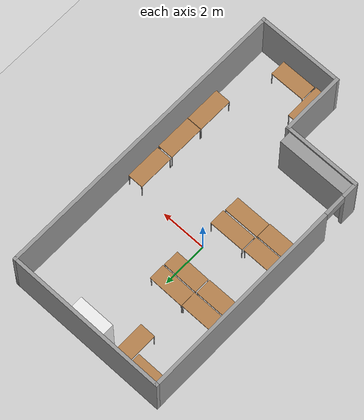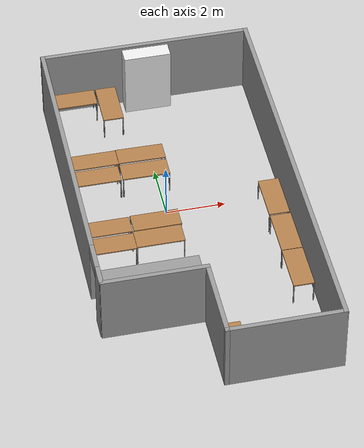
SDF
<sdf version="1.6">
 <world name="default">
  <light name="sun" type="directional">
   <pose>0 0 10 0 -0 0</pose>
   <diffuse>0.8 0.8 0.8 1</diffuse>
   <specular>0.1 0.1 0.1 1</specular>
   <attenuation>
    <range>1000</range>
    <constant>0.9</constant>
    <linear>0.01</linear>
    <quadratic>0.001</quadratic>
   </attenuation>
   <direction>-0.5 0.5 -1</direction>
  </light>
  <model name="ground_plane">
   <static>1</static>
   <link name="link">
    <collision name="collision">
     <geometry><plane><normal>0 0 1</normal><size>100 100</size></plane></geometry>
     <surface><friction><ode><mu>100</mu><mu2>50</mu2></ode></friction></surface>
    </collision>
    <visual name="visual">
     <cast_shadows>0</cast_shadows>
     <geometry><plane><normal>0 0 1</normal><size>100 100</size></plane></geometry>
     <material>
      <script><uri>file://media/materials/scripts/gazebo.material</uri><name>Gazebo/Grey</name></script>
     </material>
    </visual>
   </link>
  </model>
  <gravity>0 0 -9.8</gravity>
  <magnetic_field>6e-06 2.3e-05 -4.2e-05</magnetic_field>
  <atmosphere type="adiabatic"/>
  <physics name="default_physics" default="0" type="ode">
   <max_step_size>0.001</max_step_size>
   <real_time_factor>1</real_time_factor>
   <real_time_update_rate>1000</real_time_update_rate>
  </physics>
  <scene><ambient>0.4 0.4 0.4 1</ambient><background>0.7 0.7 0.7 1</background><shadows>1</shadows></scene>
  <spherical_coordinates>
   <surface_model>EARTH_WGS84</surface_model>
   <latitude_deg>0</latitude_deg>
   <longitude_deg>0</longitude_deg>
   <elevation>0</elevation>
   <heading_deg>0</heading_deg>
  </spherical_coordinates>
  <model name="CLF_0">
   <pose>0.46218 -0.965731 0 0 -0 0</pose>
   <link name="Wall_0">
    <pose>-3.547 1.394 0 0 0 -1.5708</pose>
    <visual name="Wall_0_Visual_0">
     <pose>-0.827428 0 1.25 0 -0 0</pose>
     <geometry><box><size>9.14514 0.15 2.5</size></box></geometry>
     <material>
      <script><uri>file://media/materials/scripts/gazebo.material</uri><name>Gazebo/Grey</name></script>
      <ambient>1 1 1 1</ambient>
     </material>
    </visual>
    <collision name="Wall_0_Collision_0">
     <geometry><box><size>9.14514 0.15 2.5</size></box></geometry>
     <pose>-0.827428 0 1.25 0 -0 0</pose>
    </collision>
    <visual name="Wall_0_Visual_1">
     <pose>5.05257 0 1.25 0 -0 0</pose>
     <geometry><box><size>0.694856 0.15 2.5</size></box></geometry>
     <material>
      <script><uri>file://media/materials/scripts/gazebo.material</uri><name>Gazebo/Grey</name></script>
      <ambient>1 1 1 1</ambient>
     </material>
    </visual>
    <collision name="Wall_0_Collision_1">
     <geometry><box><size>0.694856 0.15 2.5</size></box></geometry>
     <pose>5.05257 0 1.25 0 -0 0</pose>
    </collision>
    <visual name="Wall_0_Visual_2">
     <pose>4.22514 0 2.25 0 -0 0</pose>
     <geometry><box><size>0.96 0.15 0.5</size></box></geometry>
     <material>
      <script><uri>file://media/materials/scripts/gazebo.material</uri><name>Gazebo/Grey</name></script>
      <ambient>1 1 1 1</ambient>
     </material>
    </visual>
    <collision name="Wall_0_Collision_2">
     <geometry><box><size>0.96 0.15 0.5</size></box></geometry>
     <pose>4.22514 0 2.25 0 -0 0</pose>
    </collision>
   </link>
   <link name="Wall_10">
    <collision name="Wall_10_Collision">
     <geometry><box><size>3.5 0.15 2.5</size></box></geometry>
     <pose>0 0 1.25 0 -0 0</pose>
    </collision>
    <visual name="Wall_10_Visual">
     <pose>0 0 1.25 0 -0 0</pose>
     <geometry><box><size>3.5 0.15 2.5</size></box></geometry>
     <material>
      <script><uri>file://media/materials/scripts/gazebo.material</uri><name>Gazebo/Grey</name></script>
      <ambient>1 1 1 1</ambient>
     </material>
    </visual>
    <pose>-1.848 -4.005 0 0 -0 3.14159</pose>
   </link>
   <link name="Wall_2">
    <collision name="Wall_2_Collision">
     <geometry><box><size>7.244 0.15 2.5</size></box></geometry>
     <pose>0 0 1.25 0 -0 0</pose>
    </collision>
    <visual name="Wall_2_Visual">
     <pose>0 0 1.25 0 -0 0</pose>
     <geometry><box><size>7.244 0.15 2.5</size></box></geometry>
     <material>
      <script><uri>file://media/materials/scripts/gazebo.material</uri><name>Gazebo/Grey</name></script>
      <ambient>1 1 1 1</ambient>
     </material>
    </visual>
    <pose>0 6.719 0 0 -0 0</pose>
   </link>
   <link name="Wall_4">
    <collision name="Wall_4_Collision">
     <geometry><box><size>13.588 0.15 2.5</size></box></geometry>
     <pose>0 0 1.25 0 -0 0</pose>
    </collision>
    <visual name="Wall_4_Visual">
     <pose>0 0 1.25 0 -0 0</pose>
     <geometry><box><size>13.588 0.15 2.5</size></box></geometry>
     <material>
      <script><uri>file://media/materials/scripts/gazebo.material</uri><name>Gazebo/Grey</name></script>
      <ambient>1 1 1 1</ambient>
     </material>
    </visual>
    <pose>3.547 0 0 0 0 -1.5708</pose>
   </link>
   <link name="Wall_6">
    <collision name="Wall_6_Collision">
     <geometry><box><size>3.87 0.15 2.5</size></box></geometry>
     <pose>0 0 1.25 0 -0 0</pose>
    </collision>
    <visual name="Wall_6_Visual">
     <pose>0 0 1.25 0 -0 0</pose>
     <geometry><box><size>3.87 0.15 2.5</size></box></geometry>
     <material>
      <script><uri>file://media/materials/scripts/gazebo.material</uri><name>Gazebo/Grey</name></script>
      <ambient>1 1 1 1</ambient>
     </material>
    </visual>
    <pose>1.687 -6.719 0 0 -0 3.14159</pose>
   </link>
   <link name="Wall_8">
    <collision name="Wall_8_Collision">
     <geometry><box><size>2.864 0.15 2.5</size></box></geometry>
     <pose>0 0 1.25 0 -0 0</pose>
    </collision>
    <visual name="Wall_8_Visual">
     <pose>0 0 1.25 0 -0 0</pose>
     <geometry><box><size>2.864 0.15 2.5</size></box></geometry>
     <material>
      <script><uri>file://media/materials/scripts/gazebo.material</uri><name>Gazebo/Grey</name></script>
      <ambient>1 1 1 1</ambient>
     </material>
    </visual>
    <pose>-0.173 -5.362 0 0 -0 1.5708</pose>
   </link>
   <static>1</static>
  </model>
  <model name="clf_cabinet_1">
   <link name="link">
    <inertial>
     <mass>1</mass>
     <inertia>
      <ixx>0.166667</ixx>
      <ixy>0</ixy>
      <ixz>0</ixz>
      <iyy>0.166667</iyy>
      <iyz>0</iyz>
      <izz>0.166667</izz>
     </inertia>
    </inertial>
    <visual name="visual">
     <geometry><box><size>3.13719 0.522097 2.4</size></box></geometry>
     <material>
      <script><name>Gazebo/Grey</name><uri>file://media/materials/scripts/gazebo.material</uri></script>
      <ambient>0.3 0.3 0.3 1</ambient>
      <diffuse>0.7 0.7 0.7 1</diffuse>
      <specular>0.01 0.01 0.01 1</specular>
      <emissive>0 0 0 1</emissive>
     </material>
    </visual>
    <collision name="collision">
     <geometry><box><size>3.13719 0.522097 2.4</size></box></geometry>
     <surface>
      <friction>
       <ode><mu>1</mu><mu2>1</mu2><fdir1>0 0 0</fdir1><slip1>0</slip1><slip2>0</slip2></ode>
       <torsional>
        <coefficient>1</coefficient>
        <patch_radius>0</patch_radius>
        <surface_radius>0</surface_radius>
        <use_patch_radius>1</use_patch_radius>
        <ode><slip>0</slip></ode>
       </torsional>
      </friction>
      <bounce><restitution_coefficient>0</restitution_coefficient><threshold>1e+06</threshold></bounce>
      <contact>
       <collide_without_contact>0</collide_without_contact>
       <collide_without_contact_bitmask>1</collide_without_contact_bitmask>
       <collide_bitmask>1</collide_bitmask>
       <ode>
        <soft_cfm>0</soft_cfm>
        <soft_erp>0.2</soft_erp>
        <kp>1e+13</kp>
        <kd>1</kd>
        <max_vel>0.01</max_vel>
        <min_depth>0</min_depth>
       </ode>
       <bullet>
        <split_impulse>1</split_impulse>
        <split_impulse_penetration_threshold>-0.01</split_impulse_penetration_threshold>
        <soft_cfm>0</soft_cfm>
        <soft_erp>0.2</soft_erp>
        <kp>1e+13</kp>
        <kd>1</kd>
       </bullet>
      </contact>
     </surface>
    </collision>
   </link>
   <static>0</static>
   <pose>-1.42949 -4.63345 1.19998 -1e-06 -1.4e-05 0.000439</pose>
  </model>
  <model name="table_mod">
   <link name="link">
    <inertial>
     <inertia><ixx>1</ixx><ixy>0</ixy><ixz>0</ixz><iyy>1</iyy><iyz>0</iyz><izz>1</izz></inertia>
     <mass>1</mass>
    </inertial>
    <visual name="visual1">
     <pose>0 0 0.8 0 -0 0</pose>
     <geometry><box><size>1.6 0.7 0.04</size></box></geometry>
     <material>
      <script><uri>file://media/materials/scripts/gazebo.material</uri><name>Gazebo/Wood</name></script>
      <ambient>1 1 1 1</ambient>
      <diffuse>1 1 1 1</diffuse>
      <specular>0.2 0.2 0.2 1</specular>
      <emissive>0 0 0 1</emissive>
     </material>
    </visual>
    <visual name="front_right_leg">
     <pose>0.78 -0.33 0.4 0 -0 0</pose>
     <geometry><cylinder><radius>0.02</radius><length>0.8</length></cylinder></geometry>
     <material>
      <script><uri>file://media/materials/scripts/gazebo.material</uri><name>Gazebo/Grey</name></script>
      <ambient>0.3 0.3 0.3 1</ambient>
      <diffuse>0.7 0.7 0.7 1</diffuse>
      <specular>0.01 0.01 0.01 1</specular>
      <emissive>0 0 0 1</emissive>
     </material>
    </visual>
    <visual name="front_left_leg">
     <pose>0.78 0.33 0.4 0 -0 0</pose>
     <geometry><cylinder><radius>0.02</radius><length>0.8</length></cylinder></geometry>
     <material>
      <script><uri>file://media/materials/scripts/gazebo.material</uri><name>Gazebo/Grey</name></script>
      <ambient>0.3 0.3 0.3 1</ambient>
      <diffuse>0.7 0.7 0.7 1</diffuse>
      <specular>0.01 0.01 0.01 1</specular>
      <emissive>0 0 0 1</emissive>
     </material>
    </visual>
    <visual name="back_left_leg">
     <pose>-0.78 0.33 0.4 0 -0 0</pose>
     <geometry><cylinder><radius>0.02</radius><length>0.8</length></cylinder></geometry>
     <material>
      <script><uri>file://media/materials/scripts/gazebo.material</uri><name>Gazebo/Grey</name></script>
      <ambient>0.3 0.3 0.3 1</ambient>
      <diffuse>0.7 0.7 0.7 1</diffuse>
      <specular>0.01 0.01 0.01 1</specular>
      <emissive>0 0 0 1</emissive>
     </material>
    </visual>
    <visual name="back_right_leg">
     <pose>-0.78 -0.33 0.4 0 -0 0</pose>
     <geometry><cylinder><radius>0.02</radius><length>0.8</length></cylinder></geometry>
     <material>
      <script><uri>file://media/materials/scripts/gazebo.material</uri><name>Gazebo/Grey</name></script>
      <ambient>0.3 0.3 0.3 1</ambient>
      <diffuse>0.7 0.7 0.7 1</diffuse>
      <specular>0.01 0.01 0.01 1</specular>
      <emissive>0 0 0 1</emissive>
     </material>
    </visual>
    <collision name="surface">
     <pose>0 0 0.8 0 -0 0</pose>
     <geometry><box><size>1.6 0.7 0.03</size></box></geometry>
     <surface>
      <friction>
       <ode><mu>0.6</mu><mu2>0.6</mu2><fdir1>0 0 0</fdir1><slip1>0</slip1><slip2>0</slip2></ode>
       <torsional>
        <coefficient>1</coefficient>
        <patch_radius>0</patch_radius>
        <surface_radius>0</surface_radius>
        <use_patch_radius>1</use_patch_radius>
        <ode><slip>0</slip></ode>
       </torsional>
      </friction>
      <bounce><restitution_coefficient>0</restitution_coefficient><threshold>1e+06</threshold></bounce>
      <contact>
       <collide_without_contact>0</collide_without_contact>
       <collide_without_contact_bitmask>1</collide_without_contact_bitmask>
       <collide_bitmask>1</collide_bitmask>
       <ode>
        <soft_cfm>0</soft_cfm>
        <soft_erp>0.2</soft_erp>
        <kp>1e+13</kp>
        <kd>1</kd>
        <max_vel>0.01</max_vel>
        <min_depth>0</min_depth>
       </ode>
       <bullet>
        <split_impulse>1</split_impulse>
        <split_impulse_penetration_threshold>-0.01</split_impulse_penetration_threshold>
        <soft_cfm>0</soft_cfm>
        <soft_erp>0.2</soft_erp>
        <kp>1e+13</kp>
        <kd>1</kd>
       </bullet>
      </contact>
     </surface>
    </collision>
    <collision name="front_left_leg">
     <pose>0.78 0.33 0.4 0 -0 0</pose>
     <geometry><cylinder><radius>0.02</radius><length>0.8</length></cylinder></geometry>
     <surface>
      <friction>
       <ode><mu>1</mu><mu2>1</mu2><fdir1>0 0 0</fdir1><slip1>0</slip1><slip2>0</slip2></ode>
       <torsional>
        <coefficient>1</coefficient>
        <patch_radius>0</patch_radius>
        <surface_radius>0</surface_radius>
        <use_patch_radius>1</use_patch_radius>
        <ode><slip>0</slip></ode>
       </torsional>
      </friction>
      <bounce><restitution_coefficient>0</restitution_coefficient><threshold>1e+06</threshold></bounce>
      <contact>
       <collide_without_contact>0</collide_without_contact>
       <collide_without_contact_bitmask>1</collide_without_contact_bitmask>
       <collide_bitmask>1</collide_bitmask>
       <ode>
        <soft_cfm>0</soft_cfm>
        <soft_erp>0.2</soft_erp>
        <kp>1e+13</kp>
        <kd>1</kd>
        <max_vel>0.01</max_vel>
        <min_depth>0</min_depth>
       </ode>
       <bullet>
        <split_impulse>1</split_impulse>
        <split_impulse_penetration_threshold>-0.01</split_impulse_penetration_threshold>
        <soft_cfm>0</soft_cfm>
        <soft_erp>0.2</soft_erp>
        <kp>1e+13</kp>
        <kd>1</kd>
       </bullet>
      </contact>
     </surface>
    </collision>
    <collision name="front_right_leg">
     <pose>0.78 -0.33 0.4 0 -0 0</pose>
     <geometry><cylinder><radius>0.02</radius><length>0.8</length></cylinder></geometry>
     <surface>
      <friction>
       <ode><mu>1</mu><mu2>1</mu2><fdir1>0 0 0</fdir1><slip1>0</slip1><slip2>0</slip2></ode>
       <torsional>
        <coefficient>1</coefficient>
        <patch_radius>0</patch_radius>
        <surface_radius>0</surface_radius>
        <use_patch_radius>1</use_patch_radius>
        <ode><slip>0</slip></ode>
       </torsional>
      </friction>
      <bounce><restitution_coefficient>0</restitution_coefficient><threshold>1e+06</threshold></bounce>
      <contact>
       <collide_without_contact>0</collide_without_contact>
       <collide_without_contact_bitmask>1</collide_without_contact_bitmask>
       <collide_bitmask>1</collide_bitmask>
       <ode>
        <soft_cfm>0</soft_cfm>
        <soft_erp>0.2</soft_erp>
        <kp>1e+13</kp>
        <kd>1</kd>
        <max_vel>0.01</max_vel>
        <min_depth>0</min_depth>
       </ode>
       <bullet>
        <split_impulse>1</split_impulse>
        <split_impulse_penetration_threshold>-0.01</split_impulse_penetration_threshold>
        <soft_cfm>0</soft_cfm>
        <soft_erp>0.2</soft_erp>
        <kp>1e+13</kp>
        <kd>1</kd>
       </bullet>
      </contact>
     </surface>
    </collision>
    <collision name="back_right_leg">
     <pose>-0.78 -0.33 0.4 0 -0 0</pose>
     <geometry><cylinder><radius>0.02</radius><length>0.8</length></cylinder></geometry>
     <surface>
      <friction>
       <ode><mu>1</mu><mu2>1</mu2><fdir1>0 0 0</fdir1><slip1>0</slip1><slip2>0</slip2></ode>
       <torsional>
        <coefficient>1</coefficient>
        <patch_radius>0</patch_radius>
        <surface_radius>0</surface_radius>
        <use_patch_radius>1</use_patch_radius>
        <ode><slip>0</slip></ode>
       </torsional>
      </friction>
      <bounce><restitution_coefficient>0</restitution_coefficient><threshold>1e+06</threshold></bounce>
      <contact>
       <collide_without_contact>0</collide_without_contact>
       <collide_without_contact_bitmask>1</collide_without_contact_bitmask>
       <collide_bitmask>1</collide_bitmask>
       <ode>
        <soft_cfm>0</soft_cfm>
        <soft_erp>0.2</soft_erp>
        <kp>1e+13</kp>
        <kd>1</kd>
        <max_vel>0.01</max_vel>
        <min_depth>0</min_depth>
       </ode>
       <bullet>
        <split_impulse>1</split_impulse>
        <split_impulse_penetration_threshold>-0.01</split_impulse_penetration_threshold>
        <soft_cfm>0</soft_cfm>
        <soft_erp>0.2</soft_erp>
        <kp>1e+13</kp>
        <kd>1</kd>
       </bullet>
      </contact>
     </surface>
    </collision>
    <collision name="back_left_leg">
     <pose>-0.78 0.33 0.4 0 -0 0</pose>
     <geometry><cylinder><radius>0.02</radius><length>0.8</length></cylinder></geometry>
     <surface>
      <friction>
       <ode><mu>1</mu><mu2>1</mu2><fdir1>0 0 0</fdir1><slip1>0</slip1><slip2>0</slip2></ode>
       <torsional>
        <coefficient>1</coefficient>
        <patch_radius>0</patch_radius>
        <surface_radius>0</surface_radius>
        <use_patch_radius>1</use_patch_radius>
        <ode><slip>0</slip></ode>
       </torsional>
      </friction>
      <bounce><restitution_coefficient>0</restitution_coefficient><threshold>1e+06</threshold></bounce>
      <contact>
       <collide_without_contact>0</collide_without_contact>
       <collide_without_contact_bitmask>1</collide_without_contact_bitmask>
       <collide_bitmask>1</collide_bitmask>
       <ode>
        <soft_cfm>0</soft_cfm>
        <soft_erp>0.2</soft_erp>
        <kp>1e+13</kp>
        <kd>1</kd>
        <max_vel>0.01</max_vel>
        <min_depth>0</min_depth>
       </ode>
       <bullet>
        <split_impulse>1</split_impulse>
        <split_impulse_penetration_threshold>-0.01</split_impulse_penetration_threshold>
        <soft_cfm>0</soft_cfm>
        <soft_erp>0.2</soft_erp>
        <kp>1e+13</kp>
        <kd>1</kd>
       </bullet>
      </contact>
     </surface>
    </collision>
   </link>
   <static>0</static>
   <pose>-2.20978 -1.82153 -2.9e-05 1e-06 1e-06 -2e-06</pose>
  </model>
  <model name="table_mod_0">
   <link name="link">
    <inertial>
     <inertia><ixx>1</ixx><ixy>0</ixy><ixz>0</ixz><iyy>1</iyy><iyz>0</iyz><izz>1</izz></inertia>
     <mass>1</mass>
    </inertial>
    <visual name="visual1">
     <pose>0 0 0.8 0 -0 0</pose>
     <geometry><box><size>1.6 0.7 0.04</size></box></geometry>
     <material>
      <script><uri>file://media/materials/scripts/gazebo.material</uri><name>Gazebo/Wood</name></script>
      <ambient>1 1 1 1</ambient>
      <diffuse>1 1 1 1</diffuse>
      <specular>0.2 0.2 0.2 1</specular>
      <emissive>0 0 0 1</emissive>
     </material>
    </visual>
    <visual name="front_right_leg">
     <pose>0.78 -0.33 0.4 0 -0 0</pose>
     <geometry><cylinder><radius>0.02</radius><length>0.8</length></cylinder></geometry>
     <material>
      <script><uri>file://media/materials/scripts/gazebo.material</uri><name>Gazebo/Grey</name></script>
      <ambient>0.3 0.3 0.3 1</ambient>
      <diffuse>0.7 0.7 0.7 1</diffuse>
      <specular>0.01 0.01 0.01 1</specular>
      <emissive>0 0 0 1</emissive>
     </material>
    </visual>
    <visual name="front_left_leg">
     <pose>0.78 0.33 0.4 0 -0 0</pose>
     <geometry><cylinder><radius>0.02</radius><length>0.8</length></cylinder></geometry>
     <material>
      <script><uri>file://media/materials/scripts/gazebo.material</uri><name>Gazebo/Grey</name></script>
      <ambient>0.3 0.3 0.3 1</ambient>
      <diffuse>0.7 0.7 0.7 1</diffuse>
      <specular>0.01 0.01 0.01 1</specular>
      <emissive>0 0 0 1</emissive>
     </material>
    </visual>
    <visual name="back_left_leg">
     <pose>-0.78 0.33 0.4 0 -0 0</pose>
     <geometry><cylinder><radius>0.02</radius><length>0.8</length></cylinder></geometry>
     <material>
      <script><uri>file://media/materials/scripts/gazebo.material</uri><name>Gazebo/Grey</name></script>
      <ambient>0.3 0.3 0.3 1</ambient>
      <diffuse>0.7 0.7 0.7 1</diffuse>
      <specular>0.01 0.01 0.01 1</specular>
      <emissive>0 0 0 1</emissive>
     </material>
    </visual>
    <visual name="back_right_leg">
     <pose>-0.78 -0.33 0.4 0 -0 0</pose>
     <geometry><cylinder><radius>0.02</radius><length>0.8</length></cylinder></geometry>
     <material>
      <script><uri>file://media/materials/scripts/gazebo.material</uri><name>Gazebo/Grey</name></script>
      <ambient>0.3 0.3 0.3 1</ambient>
      <diffuse>0.7 0.7 0.7 1</diffuse>
      <specular>0.01 0.01 0.01 1</specular>
      <emissive>0 0 0 1</emissive>
     </material>
    </visual>
    <collision name="surface">
     <pose>0 0 0.8 0 -0 0</pose>
     <geometry><box><size>1.6 0.7 0.03</size></box></geometry>
     <surface>
      <friction>
       <ode><mu>0.6</mu><mu2>0.6</mu2><fdir1>0 0 0</fdir1><slip1>0</slip1><slip2>0</slip2></ode>
       <torsional>
        <coefficient>1</coefficient>
        <patch_radius>0</patch_radius>
        <surface_radius>0</surface_radius>
        <use_patch_radius>1</use_patch_radius>
        <ode><slip>0</slip></ode>
       </torsional>
      </friction>
      <bounce><restitution_coefficient>0</restitution_coefficient><threshold>1e+06</threshold></bounce>
      <contact>
       <collide_without_contact>0</collide_without_contact>
       <collide_without_contact_bitmask>1</collide_without_contact_bitmask>
       <collide_bitmask>1</collide_bitmask>
       <ode>
        <soft_cfm>0</soft_cfm>
        <soft_erp>0.2</soft_erp>
        <kp>1e+13</kp>
        <kd>1</kd>
        <max_vel>0.01</max_vel>
        <min_depth>0</min_depth>
       </ode>
       <bullet>
        <split_impulse>1</split_impulse>
        <split_impulse_penetration_threshold>-0.01</split_impulse_penetration_threshold>
        <soft_cfm>0</soft_cfm>
        <soft_erp>0.2</soft_erp>
        <kp>1e+13</kp>
        <kd>1</kd>
       </bullet>
      </contact>
     </surface>
    </collision>
    <collision name="front_left_leg">
     <pose>0.78 0.33 0.4 0 -0 0</pose>
     <geometry><cylinder><radius>0.02</radius><length>0.8</length></cylinder></geometry>
     <surface>
      <friction>
       <ode><mu>1</mu><mu2>1</mu2><fdir1>0 0 0</fdir1><slip1>0</slip1><slip2>0</slip2></ode>
       <torsional>
        <coefficient>1</coefficient>
        <patch_radius>0</patch_radius>
        <surface_radius>0</surface_radius>
        <use_patch_radius>1</use_patch_radius>
        <ode><slip>0</slip></ode>
       </torsional>
      </friction>
      <bounce><restitution_coefficient>0</restitution_coefficient><threshold>1e+06</threshold></bounce>
      <contact>
       <collide_without_contact>0</collide_without_contact>
       <collide_without_contact_bitmask>1</collide_without_contact_bitmask>
       <collide_bitmask>1</collide_bitmask>
       <ode>
        <soft_cfm>0</soft_cfm>
        <soft_erp>0.2</soft_erp>
        <kp>1e+13</kp>
        <kd>1</kd>
        <max_vel>0.01</max_vel>
        <min_depth>0</min_depth>
       </ode>
       <bullet>
        <split_impulse>1</split_impulse>
        <split_impulse_penetration_threshold>-0.01</split_impulse_penetration_threshold>
        <soft_cfm>0</soft_cfm>
        <soft_erp>0.2</soft_erp>
        <kp>1e+13</kp>
        <kd>1</kd>
       </bullet>
      </contact>
     </surface>
    </collision>
    <collision name="front_right_leg">
     <pose>0.78 -0.33 0.4 0 -0 0</pose>
     <geometry><cylinder><radius>0.02</radius><length>0.8</length></cylinder></geometry>
     <surface>
      <friction>
       <ode><mu>1</mu><mu2>1</mu2><fdir1>0 0 0</fdir1><slip1>0</slip1><slip2>0</slip2></ode>
       <torsional>
        <coefficient>1</coefficient>
        <patch_radius>0</patch_radius>
        <surface_radius>0</surface_radius>
        <use_patch_radius>1</use_patch_radius>
        <ode><slip>0</slip></ode>
       </torsional>
      </friction>
      <bounce><restitution_coefficient>0</restitution_coefficient><threshold>1e+06</threshold></bounce>
      <contact>
       <collide_without_contact>0</collide_without_contact>
       <collide_without_contact_bitmask>1</collide_without_contact_bitmask>
       <collide_bitmask>1</collide_bitmask>
       <ode>
        <soft_cfm>0</soft_cfm>
        <soft_erp>0.2</soft_erp>
        <kp>1e+13</kp>
        <kd>1</kd>
        <max_vel>0.01</max_vel>
        <min_depth>0</min_depth>
       </ode>
       <bullet>
        <split_impulse>1</split_impulse>
        <split_impulse_penetration_threshold>-0.01</split_impulse_penetration_threshold>
        <soft_cfm>0</soft_cfm>
        <soft_erp>0.2</soft_erp>
        <kp>1e+13</kp>
        <kd>1</kd>
       </bullet>
      </contact>
     </surface>
    </collision>
    <collision name="back_right_leg">
     <pose>-0.78 -0.33 0.4 0 -0 0</pose>
     <geometry><cylinder><radius>0.02</radius><length>0.8</length></cylinder></geometry>
     <surface>
      <friction>
       <ode><mu>1</mu><mu2>1</mu2><fdir1>0 0 0</fdir1><slip1>0</slip1><slip2>0</slip2></ode>
       <torsional>
        <coefficient>1</coefficient>
        <patch_radius>0</patch_radius>
        <surface_radius>0</surface_radius>
        <use_patch_radius>1</use_patch_radius>
        <ode><slip>0</slip></ode>
       </torsional>
      </friction>
      <bounce><restitution_coefficient>0</restitution_coefficient><threshold>1e+06</threshold></bounce>
      <contact>
       <collide_without_contact>0</collide_without_contact>
       <collide_without_contact_bitmask>1</collide_without_contact_bitmask>
       <collide_bitmask>1</collide_bitmask>
       <ode>
        <soft_cfm>0</soft_cfm>
        <soft_erp>0.2</soft_erp>
        <kp>1e+13</kp>
        <kd>1</kd>
        <max_vel>0.01</max_vel>
        <min_depth>0</min_depth>
       </ode>
       <bullet>
        <split_impulse>1</split_impulse>
        <split_impulse_penetration_threshold>-0.01</split_impulse_penetration_threshold>
        <soft_cfm>0</soft_cfm>
        <soft_erp>0.2</soft_erp>
        <kp>1e+13</kp>
        <kd>1</kd>
       </bullet>
      </contact>
     </surface>
    </collision>
    <collision name="back_left_leg">
     <pose>-0.78 0.33 0.4 0 -0 0</pose>
     <geometry><cylinder><radius>0.02</radius><length>0.8</length></cylinder></geometry>
     <surface>
      <friction>
       <ode><mu>1</mu><mu2>1</mu2><fdir1>0 0 0</fdir1><slip1>0</slip1><slip2>0</slip2></ode>
       <torsional>
        <coefficient>1</coefficient>
        <patch_radius>0</patch_radius>
        <surface_radius>0</surface_radius>
        <use_patch_radius>1</use_patch_radius>
        <ode><slip>0</slip></ode>
       </torsional>
      </friction>
      <bounce><restitution_coefficient>0</restitution_coefficient><threshold>1e+06</threshold></bounce>
      <contact>
       <collide_without_contact>0</collide_without_contact>
       <collide_without_contact_bitmask>1</collide_without_contact_bitmask>
       <collide_bitmask>1</collide_bitmask>
       <ode>
        <soft_cfm>0</soft_cfm>
        <soft_erp>0.2</soft_erp>
        <kp>1e+13</kp>
        <kd>1</kd>
        <max_vel>0.01</max_vel>
        <min_depth>0</min_depth>
       </ode>
       <bullet>
        <split_impulse>1</split_impulse>
        <split_impulse_penetration_threshold>-0.01</split_impulse_penetration_threshold>
        <soft_cfm>0</soft_cfm>
        <soft_erp>0.2</soft_erp>
        <kp>1e+13</kp>
        <kd>1</kd>
       </bullet>
      </contact>
     </surface>
    </collision>
   </link>
   <static>0</static>
   <pose>-0.609391 -1.75257 0.015325 0.043779 2.2e-05 0.001206</pose>
  </model>
  <model name="table_mod_clone">
   <link name="link">
    <inertial>
     <inertia><ixx>1</ixx><ixy>0</ixy><ixz>0</ixz><iyy>1</iyy><iyz>0</iyz><izz>1</izz></inertia>
     <mass>1</mass>
    </inertial>
    <visual name="visual1">
     <pose>0 0 0.8 0 -0 0</pose>
     <geometry><box><size>1.6 0.7 0.04</size></box></geometry>
     <material>
      <script><uri>file://media/materials/scripts/gazebo.material</uri><name>Gazebo/Wood</name></script>
      <ambient>1 1 1 1</ambient>
      <diffuse>1 1 1 1</diffuse>
      <specular>0.2 0.2 0.2 1</specular>
      <emissive>0 0 0 1</emissive>
     </material>
    </visual>
    <visual name="front_right_leg">
     <pose>0.78 -0.33 0.4 0 -0 0</pose>
     <geometry><cylinder><radius>0.02</radius><length>0.8</length></cylinder></geometry>
     <material>
      <script><uri>file://media/materials/scripts/gazebo.material</uri><name>Gazebo/Grey</name></script>
      <ambient>0.3 0.3 0.3 1</ambient>
      <diffuse>0.7 0.7 0.7 1</diffuse>
      <specular>0.01 0.01 0.01 1</specular>
      <emissive>0 0 0 1</emissive>
     </material>
    </visual>
    <visual name="front_left_leg">
     <pose>0.78 0.33 0.4 0 -0 0</pose>
     <geometry><cylinder><radius>0.02</radius><length>0.8</length></cylinder></geometry>
     <material>
      <script><uri>file://media/materials/scripts/gazebo.material</uri><name>Gazebo/Grey</name></script>
      <ambient>0.3 0.3 0.3 1</ambient>
      <diffuse>0.7 0.7 0.7 1</diffuse>
      <specular>0.01 0.01 0.01 1</specular>
      <emissive>0 0 0 1</emissive>
     </material>
    </visual>
    <visual name="back_left_leg">
     <pose>-0.78 0.33 0.4 0 -0 0</pose>
     <geometry><cylinder><radius>0.02</radius><length>0.8</length></cylinder></geometry>
     <material>
      <script><uri>file://media/materials/scripts/gazebo.material</uri><name>Gazebo/Grey</name></script>
      <ambient>0.3 0.3 0.3 1</ambient>
      <diffuse>0.7 0.7 0.7 1</diffuse>
      <specular>0.01 0.01 0.01 1</specular>
      <emissive>0 0 0 1</emissive>
     </material>
    </visual>
    <visual name="back_right_leg">
     <pose>-0.78 -0.33 0.4 0 -0 0</pose>
     <geometry><cylinder><radius>0.02</radius><length>0.8</length></cylinder></geometry>
     <material>
      <script><uri>file://media/materials/scripts/gazebo.material</uri><name>Gazebo/Grey</name></script>
      <ambient>0.3 0.3 0.3 1</ambient>
      <diffuse>0.7 0.7 0.7 1</diffuse>
      <specular>0.01 0.01 0.01 1</specular>
      <emissive>0 0 0 1</emissive>
     </material>
    </visual>
    <collision name="surface">
     <pose>0 0 0.8 0 -0 0</pose>
     <geometry><box><size>1.6 0.7 0.03</size></box></geometry>
     <surface>
      <friction>
       <ode><mu>0.6</mu><mu2>0.6</mu2><fdir1>0 0 0</fdir1><slip1>0</slip1><slip2>0</slip2></ode>
       <torsional>
        <coefficient>1</coefficient>
        <patch_radius>0</patch_radius>
        <surface_radius>0</surface_radius>
        <use_patch_radius>1</use_patch_radius>
        <ode><slip>0</slip></ode>
       </torsional>
      </friction>
      <bounce><restitution_coefficient>0</restitution_coefficient><threshold>1e+06</threshold></bounce>
      <contact>
       <collide_without_contact>0</collide_without_contact>
       <collide_without_contact_bitmask>1</collide_without_contact_bitmask>
       <collide_bitmask>1</collide_bitmask>
       <ode>
        <soft_cfm>0</soft_cfm>
        <soft_erp>0.2</soft_erp>
        <kp>1e+13</kp>
        <kd>1</kd>
        <max_vel>0.01</max_vel>
        <min_depth>0</min_depth>
       </ode>
       <bullet>
        <split_impulse>1</split_impulse>
        <split_impulse_penetration_threshold>-0.01</split_impulse_penetration_threshold>
        <soft_cfm>0</soft_cfm>
        <soft_erp>0.2</soft_erp>
        <kp>1e+13</kp>
        <kd>1</kd>
       </bullet>
      </contact>
     </surface>
    </collision>
    <collision name="front_left_leg">
     <pose>0.78 0.33 0.4 0 -0 0</pose>
     <geometry><cylinder><radius>0.02</radius><length>0.8</length></cylinder></geometry>
     <surface>
      <friction>
       <ode><mu>1</mu><mu2>1</mu2><fdir1>0 0 0</fdir1><slip1>0</slip1><slip2>0</slip2></ode>
       <torsional>
        <coefficient>1</coefficient>
        <patch_radius>0</patch_radius>
        <surface_radius>0</surface_radius>
        <use_patch_radius>1</use_patch_radius>
        <ode><slip>0</slip></ode>
       </torsional>
      </friction>
      <bounce><restitution_coefficient>0</restitution_coefficient><threshold>1e+06</threshold></bounce>
      <contact>
       <collide_without_contact>0</collide_without_contact>
       <collide_without_contact_bitmask>1</collide_without_contact_bitmask>
       <collide_bitmask>1</collide_bitmask>
       <ode>
        <soft_cfm>0</soft_cfm>
        <soft_erp>0.2</soft_erp>
        <kp>1e+13</kp>
        <kd>1</kd>
        <max_vel>0.01</max_vel>
        <min_depth>0</min_depth>
       </ode>
       <bullet>
        <split_impulse>1</split_impulse>
        <split_impulse_penetration_threshold>-0.01</split_impulse_penetration_threshold>
        <soft_cfm>0</soft_cfm>
        <soft_erp>0.2</soft_erp>
        <kp>1e+13</kp>
        <kd>1</kd>
       </bullet>
      </contact>
     </surface>
    </collision>
    <collision name="front_right_leg">
     <pose>0.78 -0.33 0.4 0 -0 0</pose>
     <geometry><cylinder><radius>0.02</radius><length>0.8</length></cylinder></geometry>
     <surface>
      <friction>
       <ode><mu>1</mu><mu2>1</mu2><fdir1>0 0 0</fdir1><slip1>0</slip1><slip2>0</slip2></ode>
       <torsional>
        <coefficient>1</coefficient>
        <patch_radius>0</patch_radius>
        <surface_radius>0</surface_radius>
        <use_patch_radius>1</use_patch_radius>
        <ode><slip>0</slip></ode>
       </torsional>
      </friction>
      <bounce><restitution_coefficient>0</restitution_coefficient><threshold>1e+06</threshold></bounce>
      <contact>
       <collide_without_contact>0</collide_without_contact>
       <collide_without_contact_bitmask>1</collide_without_contact_bitmask>
       <collide_bitmask>1</collide_bitmask>
       <ode>
        <soft_cfm>0</soft_cfm>
        <soft_erp>0.2</soft_erp>
        <kp>1e+13</kp>
        <kd>1</kd>
        <max_vel>0.01</max_vel>
        <min_depth>0</min_depth>
       </ode>
       <bullet>
        <split_impulse>1</split_impulse>
        <split_impulse_penetration_threshold>-0.01</split_impulse_penetration_threshold>
        <soft_cfm>0</soft_cfm>
        <soft_erp>0.2</soft_erp>
        <kp>1e+13</kp>
        <kd>1</kd>
       </bullet>
      </contact>
     </surface>
    </collision>
    <collision name="back_right_leg">
     <pose>-0.78 -0.33 0.4 0 -0 0</pose>
     <geometry><cylinder><radius>0.02</radius><length>0.8</length></cylinder></geometry>
     <surface>
      <friction>
       <ode><mu>1</mu><mu2>1</mu2><fdir1>0 0 0</fdir1><slip1>0</slip1><slip2>0</slip2></ode>
       <torsional>
        <coefficient>1</coefficient>
        <patch_radius>0</patch_radius>
        <surface_radius>0</surface_radius>
        <use_patch_radius>1</use_patch_radius>
        <ode><slip>0</slip></ode>
       </torsional>
      </friction>
      <bounce><restitution_coefficient>0</restitution_coefficient><threshold>1e+06</threshold></bounce>
      <contact>
       <collide_without_contact>0</collide_without_contact>
       <collide_without_contact_bitmask>1</collide_without_contact_bitmask>
       <collide_bitmask>1</collide_bitmask>
       <ode>
        <soft_cfm>0</soft_cfm>
        <soft_erp>0.2</soft_erp>
        <kp>1e+13</kp>
        <kd>1</kd>
        <max_vel>0.01</max_vel>
        <min_depth>0</min_depth>
       </ode>
       <bullet>
        <split_impulse>1</split_impulse>
        <split_impulse_penetration_threshold>-0.01</split_impulse_penetration_threshold>
        <soft_cfm>0</soft_cfm>
        <soft_erp>0.2</soft_erp>
        <kp>1e+13</kp>
        <kd>1</kd>
       </bullet>
      </contact>
     </surface>
    </collision>
    <collision name="back_left_leg">
     <pose>-0.78 0.33 0.4 0 -0 0</pose>
     <geometry><cylinder><radius>0.02</radius><length>0.8</length></cylinder></geometry>
     <surface>
      <friction>
       <ode><mu>1</mu><mu2>1</mu2><fdir1>0 0 0</fdir1><slip1>0</slip1><slip2>0</slip2></ode>
       <torsional>
        <coefficient>1</coefficient>
        <patch_radius>0</patch_radius>
        <surface_radius>0</surface_radius>
        <use_patch_radius>1</use_patch_radius>
        <ode><slip>0</slip></ode>
       </torsional>
      </friction>
      <bounce><restitution_coefficient>0</restitution_coefficient><threshold>1e+06</threshold></bounce>
      <contact>
       <collide_without_contact>0</collide_without_contact>
       <collide_without_contact_bitmask>1</collide_without_contact_bitmask>
       <collide_bitmask>1</collide_bitmask>
       <ode>
        <soft_cfm>0</soft_cfm>
        <soft_erp>0.2</soft_erp>
        <kp>1e+13</kp>
        <kd>1</kd>
        <max_vel>0.01</max_vel>
        <min_depth>0</min_depth>
       </ode>
       <bullet>
        <split_impulse>1</split_impulse>
        <split_impulse_penetration_threshold>-0.01</split_impulse_penetration_threshold>
        <soft_cfm>0</soft_cfm>
        <soft_erp>0.2</soft_erp>
        <kp>1e+13</kp>
        <kd>1</kd>
       </bullet>
      </contact>
     </surface>
    </collision>
   </link>
   <static>0</static>
   <pose>-2.20983 -1.10049 0.015295 -0.043718 -0 -3e-06</pose>
  </model>
  <model name="table_mod_clone_0">
   <link name="link">
    <inertial>
     <inertia><ixx>1</ixx><ixy>0</ixy><ixz>0</ixz><iyy>1</iyy><iyz>0</iyz><izz>1</izz></inertia>
     <mass>1</mass>
    </inertial>
    <visual name="visual1">
     <pose>0 0 0.8 0 -0 0</pose>
     <geometry><box><size>1.6 0.7 0.04</size></box></geometry>
     <material>
      <script><uri>file://media/materials/scripts/gazebo.material</uri><name>Gazebo/Wood</name></script>
      <ambient>1 1 1 1</ambient>
      <diffuse>1 1 1 1</diffuse>
      <specular>0.2 0.2 0.2 1</specular>
      <emissive>0 0 0 1</emissive>
     </material>
    </visual>
    <visual name="front_right_leg">
     <pose>0.78 -0.33 0.4 0 -0 0</pose>
     <geometry><cylinder><radius>0.02</radius><length>0.8</length></cylinder></geometry>
     <material>
      <script><uri>file://media/materials/scripts/gazebo.material</uri><name>Gazebo/Grey</name></script>
      <ambient>0.3 0.3 0.3 1</ambient>
      <diffuse>0.7 0.7 0.7 1</diffuse>
      <specular>0.01 0.01 0.01 1</specular>
      <emissive>0 0 0 1</emissive>
     </material>
    </visual>
    <visual name="front_left_leg">
     <pose>0.78 0.33 0.4 0 -0 0</pose>
     <geometry><cylinder><radius>0.02</radius><length>0.8</length></cylinder></geometry>
     <material>
      <script><uri>file://media/materials/scripts/gazebo.material</uri><name>Gazebo/Grey</name></script>
      <ambient>0.3 0.3 0.3 1</ambient>
      <diffuse>0.7 0.7 0.7 1</diffuse>
      <specular>0.01 0.01 0.01 1</specular>
      <emissive>0 0 0 1</emissive>
     </material>
    </visual>
    <visual name="back_left_leg">
     <pose>-0.78 0.33 0.4 0 -0 0</pose>
     <geometry><cylinder><radius>0.02</radius><length>0.8</length></cylinder></geometry>
     <material>
      <script><uri>file://media/materials/scripts/gazebo.material</uri><name>Gazebo/Grey</name></script>
      <ambient>0.3 0.3 0.3 1</ambient>
      <diffuse>0.7 0.7 0.7 1</diffuse>
      <specular>0.01 0.01 0.01 1</specular>
      <emissive>0 0 0 1</emissive>
     </material>
    </visual>
    <visual name="back_right_leg">
     <pose>-0.78 -0.33 0.4 0 -0 0</pose>
     <geometry><cylinder><radius>0.02</radius><length>0.8</length></cylinder></geometry>
     <material>
      <script><uri>file://media/materials/scripts/gazebo.material</uri><name>Gazebo/Grey</name></script>
      <ambient>0.3 0.3 0.3 1</ambient>
      <diffuse>0.7 0.7 0.7 1</diffuse>
      <specular>0.01 0.01 0.01 1</specular>
      <emissive>0 0 0 1</emissive>
     </material>
    </visual>
    <collision name="surface">
     <pose>0 0 0.8 0 -0 0</pose>
     <geometry><box><size>1.6 0.7 0.03</size></box></geometry>
     <surface>
      <friction>
       <ode><mu>0.6</mu><mu2>0.6</mu2><fdir1>0 0 0</fdir1><slip1>0</slip1><slip2>0</slip2></ode>
       <torsional>
        <coefficient>1</coefficient>
        <patch_radius>0</patch_radius>
        <surface_radius>0</surface_radius>
        <use_patch_radius>1</use_patch_radius>
        <ode><slip>0</slip></ode>
       </torsional>
      </friction>
      <bounce><restitution_coefficient>0</restitution_coefficient><threshold>1e+06</threshold></bounce>
      <contact>
       <collide_without_contact>0</collide_without_contact>
       <collide_without_contact_bitmask>1</collide_without_contact_bitmask>
       <collide_bitmask>1</collide_bitmask>
       <ode>
        <soft_cfm>0</soft_cfm>
        <soft_erp>0.2</soft_erp>
        <kp>1e+13</kp>
        <kd>1</kd>
        <max_vel>0.01</max_vel>
        <min_depth>0</min_depth>
       </ode>
       <bullet>
        <split_impulse>1</split_impulse>
        <split_impulse_penetration_threshold>-0.01</split_impulse_penetration_threshold>
        <soft_cfm>0</soft_cfm>
        <soft_erp>0.2</soft_erp>
        <kp>1e+13</kp>
        <kd>1</kd>
       </bullet>
      </contact>
     </surface>
    </collision>
    <collision name="front_left_leg">
     <pose>0.78 0.33 0.4 0 -0 0</pose>
     <geometry><cylinder><radius>0.02</radius><length>0.8</length></cylinder></geometry>
     <surface>
      <friction>
       <ode><mu>1</mu><mu2>1</mu2><fdir1>0 0 0</fdir1><slip1>0</slip1><slip2>0</slip2></ode>
       <torsional>
        <coefficient>1</coefficient>
        <patch_radius>0</patch_radius>
        <surface_radius>0</surface_radius>
        <use_patch_radius>1</use_patch_radius>
        <ode><slip>0</slip></ode>
       </torsional>
      </friction>
      <bounce><restitution_coefficient>0</restitution_coefficient><threshold>1e+06</threshold></bounce>
      <contact>
       <collide_without_contact>0</collide_without_contact>
       <collide_without_contact_bitmask>1</collide_without_contact_bitmask>
       <collide_bitmask>1</collide_bitmask>
       <ode>
        <soft_cfm>0</soft_cfm>
        <soft_erp>0.2</soft_erp>
        <kp>1e+13</kp>
        <kd>1</kd>
        <max_vel>0.01</max_vel>
        <min_depth>0</min_depth>
       </ode>
       <bullet>
        <split_impulse>1</split_impulse>
        <split_impulse_penetration_threshold>-0.01</split_impulse_penetration_threshold>
        <soft_cfm>0</soft_cfm>
        <soft_erp>0.2</soft_erp>
        <kp>1e+13</kp>
        <kd>1</kd>
       </bullet>
      </contact>
     </surface>
    </collision>
    <collision name="front_right_leg">
     <pose>0.78 -0.33 0.4 0 -0 0</pose>
     <geometry><cylinder><radius>0.02</radius><length>0.8</length></cylinder></geometry>
     <surface>
      <friction>
       <ode><mu>1</mu><mu2>1</mu2><fdir1>0 0 0</fdir1><slip1>0</slip1><slip2>0</slip2></ode>
       <torsional>
        <coefficient>1</coefficient>
        <patch_radius>0</patch_radius>
        <surface_radius>0</surface_radius>
        <use_patch_radius>1</use_patch_radius>
        <ode><slip>0</slip></ode>
       </torsional>
      </friction>
      <bounce><restitution_coefficient>0</restitution_coefficient><threshold>1e+06</threshold></bounce>
      <contact>
       <collide_without_contact>0</collide_without_contact>
       <collide_without_contact_bitmask>1</collide_without_contact_bitmask>
       <collide_bitmask>1</collide_bitmask>
       <ode>
        <soft_cfm>0</soft_cfm>
        <soft_erp>0.2</soft_erp>
        <kp>1e+13</kp>
        <kd>1</kd>
        <max_vel>0.01</max_vel>
        <min_depth>0</min_depth>
       </ode>
       <bullet>
        <split_impulse>1</split_impulse>
        <split_impulse_penetration_threshold>-0.01</split_impulse_penetration_threshold>
        <soft_cfm>0</soft_cfm>
        <soft_erp>0.2</soft_erp>
        <kp>1e+13</kp>
        <kd>1</kd>
       </bullet>
      </contact>
     </surface>
    </collision>
    <collision name="back_right_leg">
     <pose>-0.78 -0.33 0.4 0 -0 0</pose>
     <geometry><cylinder><radius>0.02</radius><length>0.8</length></cylinder></geometry>
     <surface>
      <friction>
       <ode><mu>1</mu><mu2>1</mu2><fdir1>0 0 0</fdir1><slip1>0</slip1><slip2>0</slip2></ode>
       <torsional>
        <coefficient>1</coefficient>
        <patch_radius>0</patch_radius>
        <surface_radius>0</surface_radius>
        <use_patch_radius>1</use_patch_radius>
        <ode><slip>0</slip></ode>
       </torsional>
      </friction>
      <bounce><restitution_coefficient>0</restitution_coefficient><threshold>1e+06</threshold></bounce>
      <contact>
       <collide_without_contact>0</collide_without_contact>
       <collide_without_contact_bitmask>1</collide_without_contact_bitmask>
       <collide_bitmask>1</collide_bitmask>
       <ode>
        <soft_cfm>0</soft_cfm>
        <soft_erp>0.2</soft_erp>
        <kp>1e+13</kp>
        <kd>1</kd>
        <max_vel>0.01</max_vel>
        <min_depth>0</min_depth>
       </ode>
       <bullet>
        <split_impulse>1</split_impulse>
        <split_impulse_penetration_threshold>-0.01</split_impulse_penetration_threshold>
        <soft_cfm>0</soft_cfm>
        <soft_erp>0.2</soft_erp>
        <kp>1e+13</kp>
        <kd>1</kd>
       </bullet>
      </contact>
     </surface>
    </collision>
    <collision name="back_left_leg">
     <pose>-0.78 0.33 0.4 0 -0 0</pose>
     <geometry><cylinder><radius>0.02</radius><length>0.8</length></cylinder></geometry>
     <surface>
      <friction>
       <ode><mu>1</mu><mu2>1</mu2><fdir1>0 0 0</fdir1><slip1>0</slip1><slip2>0</slip2></ode>
       <torsional>
        <coefficient>1</coefficient>
        <patch_radius>0</patch_radius>
        <surface_radius>0</surface_radius>
        <use_patch_radius>1</use_patch_radius>
        <ode><slip>0</slip></ode>
       </torsional>
      </friction>
      <bounce><restitution_coefficient>0</restitution_coefficient><threshold>1e+06</threshold></bounce>
      <contact>
       <collide_without_contact>0</collide_without_contact>
       <collide_without_contact_bitmask>1</collide_without_contact_bitmask>
       <collide_bitmask>1</collide_bitmask>
       <ode>
        <soft_cfm>0</soft_cfm>
        <soft_erp>0.2</soft_erp>
        <kp>1e+13</kp>
        <kd>1</kd>
        <max_vel>0.01</max_vel>
        <min_depth>0</min_depth>
       </ode>
       <bullet>
        <split_impulse>1</split_impulse>
        <split_impulse_penetration_threshold>-0.01</split_impulse_penetration_threshold>
        <soft_cfm>0</soft_cfm>
        <soft_erp>0.2</soft_erp>
        <kp>1e+13</kp>
        <kd>1</kd>
       </bullet>
      </contact>
     </surface>
    </collision>
   </link>
   <static>0</static>
   <pose>-0.564494 -1.03214 0 0 -0 0.002157</pose>
  </model>
  <model name="table_mod_1">
   <link name="link">
    <inertial>
     <inertia><ixx>1</ixx><ixy>0</ixy><ixz>0</ixz><iyy>1</iyy><iyz>0</iyz><izz>1</izz></inertia>
     <mass>1</mass>
    </inertial>
    <visual name="visual1">
     <pose>0 0 0.8 0 -0 0</pose>
     <geometry><box><size>1.6 0.7 0.04</size></box></geometry>
     <material>
      <script><uri>file://media/materials/scripts/gazebo.material</uri><name>Gazebo/Wood</name></script>
      <ambient>1 1 1 1</ambient>
      <diffuse>1 1 1 1</diffuse>
      <specular>0.2 0.2 0.2 1</specular>
      <emissive>0 0 0 1</emissive>
     </material>
    </visual>
    <visual name="front_right_leg">
     <pose>0.78 -0.33 0.4 0 -0 0</pose>
     <geometry><cylinder><radius>0.02</radius><length>0.8</length></cylinder></geometry>
     <material>
      <script><uri>file://media/materials/scripts/gazebo.material</uri><name>Gazebo/Grey</name></script>
      <ambient>0.3 0.3 0.3 1</ambient>
      <diffuse>0.7 0.7 0.7 1</diffuse>
      <specular>0.01 0.01 0.01 1</specular>
      <emissive>0 0 0 1</emissive>
     </material>
    </visual>
    <visual name="front_left_leg">
     <pose>0.78 0.33 0.4 0 -0 0</pose>
     <geometry><cylinder><radius>0.02</radius><length>0.8</length></cylinder></geometry>
     <material>
      <script><uri>file://media/materials/scripts/gazebo.material</uri><name>Gazebo/Grey</name></script>
      <ambient>0.3 0.3 0.3 1</ambient>
      <diffuse>0.7 0.7 0.7 1</diffuse>
      <specular>0.01 0.01 0.01 1</specular>
      <emissive>0 0 0 1</emissive>
     </material>
    </visual>
    <visual name="back_left_leg">
     <pose>-0.78 0.33 0.4 0 -0 0</pose>
     <geometry><cylinder><radius>0.02</radius><length>0.8</length></cylinder></geometry>
     <material>
      <script><uri>file://media/materials/scripts/gazebo.material</uri><name>Gazebo/Grey</name></script>
      <ambient>0.3 0.3 0.3 1</ambient>
      <diffuse>0.7 0.7 0.7 1</diffuse>
      <specular>0.01 0.01 0.01 1</specular>
      <emissive>0 0 0 1</emissive>
     </material>
    </visual>
    <visual name="back_right_leg">
     <pose>-0.78 -0.33 0.4 0 -0 0</pose>
     <geometry><cylinder><radius>0.02</radius><length>0.8</length></cylinder></geometry>
     <material>
      <script><uri>file://media/materials/scripts/gazebo.material</uri><name>Gazebo/Grey</name></script>
      <ambient>0.3 0.3 0.3 1</ambient>
      <diffuse>0.7 0.7 0.7 1</diffuse>
      <specular>0.01 0.01 0.01 1</specular>
      <emissive>0 0 0 1</emissive>
     </material>
    </visual>
    <collision name="surface">
     <pose>0 0 0.8 0 -0 0</pose>
     <geometry><box><size>1.6 0.7 0.03</size></box></geometry>
     <surface>
      <friction>
       <ode><mu>0.6</mu><mu2>0.6</mu2><fdir1>0 0 0</fdir1><slip1>0</slip1><slip2>0</slip2></ode>
       <torsional>
        <coefficient>1</coefficient>
        <patch_radius>0</patch_radius>
        <surface_radius>0</surface_radius>
        <use_patch_radius>1</use_patch_radius>
        <ode><slip>0</slip></ode>
       </torsional>
      </friction>
      <bounce><restitution_coefficient>0</restitution_coefficient><threshold>1e+06</threshold></bounce>
      <contact>
       <collide_without_contact>0</collide_without_contact>
       <collide_without_contact_bitmask>1</collide_without_contact_bitmask>
       <collide_bitmask>1</collide_bitmask>
       <ode>
        <soft_cfm>0</soft_cfm>
        <soft_erp>0.2</soft_erp>
        <kp>1e+13</kp>
        <kd>1</kd>
        <max_vel>0.01</max_vel>
        <min_depth>0</min_depth>
       </ode>
       <bullet>
        <split_impulse>1</split_impulse>
        <split_impulse_penetration_threshold>-0.01</split_impulse_penetration_threshold>
        <soft_cfm>0</soft_cfm>
        <soft_erp>0.2</soft_erp>
        <kp>1e+13</kp>
        <kd>1</kd>
       </bullet>
      </contact>
     </surface>
    </collision>
    <collision name="front_left_leg">
     <pose>0.78 0.33 0.4 0 -0 0</pose>
     <geometry><cylinder><radius>0.02</radius><length>0.8</length></cylinder></geometry>
     <surface>
      <friction>
       <ode><mu>1</mu><mu2>1</mu2><fdir1>0 0 0</fdir1><slip1>0</slip1><slip2>0</slip2></ode>
       <torsional>
        <coefficient>1</coefficient>
        <patch_radius>0</patch_radius>
        <surface_radius>0</surface_radius>
        <use_patch_radius>1</use_patch_radius>
        <ode><slip>0</slip></ode>
       </torsional>
      </friction>
      <bounce><restitution_coefficient>0</restitution_coefficient><threshold>1e+06</threshold></bounce>
      <contact>
       <collide_without_contact>0</collide_without_contact>
       <collide_without_contact_bitmask>1</collide_without_contact_bitmask>
       <collide_bitmask>1</collide_bitmask>
       <ode>
        <soft_cfm>0</soft_cfm>
        <soft_erp>0.2</soft_erp>
        <kp>1e+13</kp>
        <kd>1</kd>
        <max_vel>0.01</max_vel>
        <min_depth>0</min_depth>
       </ode>
       <bullet>
        <split_impulse>1</split_impulse>
        <split_impulse_penetration_threshold>-0.01</split_impulse_penetration_threshold>
        <soft_cfm>0</soft_cfm>
        <soft_erp>0.2</soft_erp>
        <kp>1e+13</kp>
        <kd>1</kd>
       </bullet>
      </contact>
     </surface>
    </collision>
    <collision name="front_right_leg">
     <pose>0.78 -0.33 0.4 0 -0 0</pose>
     <geometry><cylinder><radius>0.02</radius><length>0.8</length></cylinder></geometry>
     <surface>
      <friction>
       <ode><mu>1</mu><mu2>1</mu2><fdir1>0 0 0</fdir1><slip1>0</slip1><slip2>0</slip2></ode>
       <torsional>
        <coefficient>1</coefficient>
        <patch_radius>0</patch_radius>
        <surface_radius>0</surface_radius>
        <use_patch_radius>1</use_patch_radius>
        <ode><slip>0</slip></ode>
       </torsional>
      </friction>
      <bounce><restitution_coefficient>0</restitution_coefficient><threshold>1e+06</threshold></bounce>
      <contact>
       <collide_without_contact>0</collide_without_contact>
       <collide_without_contact_bitmask>1</collide_without_contact_bitmask>
       <collide_bitmask>1</collide_bitmask>
       <ode>
        <soft_cfm>0</soft_cfm>
        <soft_erp>0.2</soft_erp>
        <kp>1e+13</kp>
        <kd>1</kd>
        <max_vel>0.01</max_vel>
        <min_depth>0</min_depth>
       </ode>
       <bullet>
        <split_impulse>1</split_impulse>
        <split_impulse_penetration_threshold>-0.01</split_impulse_penetration_threshold>
        <soft_cfm>0</soft_cfm>
        <soft_erp>0.2</soft_erp>
        <kp>1e+13</kp>
        <kd>1</kd>
       </bullet>
      </contact>
     </surface>
    </collision>
    <collision name="back_right_leg">
     <pose>-0.78 -0.33 0.4 0 -0 0</pose>
     <geometry><cylinder><radius>0.02</radius><length>0.8</length></cylinder></geometry>
     <surface>
      <friction>
       <ode><mu>1</mu><mu2>1</mu2><fdir1>0 0 0</fdir1><slip1>0</slip1><slip2>0</slip2></ode>
       <torsional>
        <coefficient>1</coefficient>
        <patch_radius>0</patch_radius>
        <surface_radius>0</surface_radius>
        <use_patch_radius>1</use_patch_radius>
        <ode><slip>0</slip></ode>
       </torsional>
      </friction>
      <bounce><restitution_coefficient>0</restitution_coefficient><threshold>1e+06</threshold></bounce>
      <contact>
       <collide_without_contact>0</collide_without_contact>
       <collide_without_contact_bitmask>1</collide_without_contact_bitmask>
       <collide_bitmask>1</collide_bitmask>
       <ode>
        <soft_cfm>0</soft_cfm>
        <soft_erp>0.2</soft_erp>
        <kp>1e+13</kp>
        <kd>1</kd>
        <max_vel>0.01</max_vel>
        <min_depth>0</min_depth>
       </ode>
       <bullet>
        <split_impulse>1</split_impulse>
        <split_impulse_penetration_threshold>-0.01</split_impulse_penetration_threshold>
        <soft_cfm>0</soft_cfm>
        <soft_erp>0.2</soft_erp>
        <kp>1e+13</kp>
        <kd>1</kd>
       </bullet>
      </contact>
     </surface>
    </collision>
    <collision name="back_left_leg">
     <pose>-0.78 0.33 0.4 0 -0 0</pose>
     <geometry><cylinder><radius>0.02</radius><length>0.8</length></cylinder></geometry>
     <surface>
      <friction>
       <ode><mu>1</mu><mu2>1</mu2><fdir1>0 0 0</fdir1><slip1>0</slip1><slip2>0</slip2></ode>
       <torsional>
        <coefficient>1</coefficient>
        <patch_radius>0</patch_radius>
        <surface_radius>0</surface_radius>
        <use_patch_radius>1</use_patch_radius>
        <ode><slip>0</slip></ode>
       </torsional>
      </friction>
      <bounce><restitution_coefficient>0</restitution_coefficient><threshold>1e+06</threshold></bounce>
      <contact>
       <collide_without_contact>0</collide_without_contact>
       <collide_without_contact_bitmask>1</collide_without_contact_bitmask>
       <collide_bitmask>1</collide_bitmask>
       <ode>
        <soft_cfm>0</soft_cfm>
        <soft_erp>0.2</soft_erp>
        <kp>1e+13</kp>
        <kd>1</kd>
        <max_vel>0.01</max_vel>
        <min_depth>0</min_depth>
       </ode>
       <bullet>
        <split_impulse>1</split_impulse>
        <split_impulse_penetration_threshold>-0.01</split_impulse_penetration_threshold>
        <soft_cfm>0</soft_cfm>
        <soft_erp>0.2</soft_erp>
        <kp>1e+13</kp>
        <kd>1</kd>
       </bullet>
      </contact>
     </surface>
    </collision>
   </link>
   <static>0</static>
   <pose>-2.09962 1.37366 -3e-06 0 4e-06 0.000265</pose>
  </model>
  <model name="table_mod_2">
   <link name="link">
    <inertial>
     <inertia><ixx>1</ixx><ixy>0</ixy><ixz>0</ixz><iyy>1</iyy><iyz>0</iyz><izz>1</izz></inertia>
     <mass>1</mass>
    </inertial>
    <visual name="visual1">
     <pose>0 0 0.8 0 -0 0</pose>
     <geometry><box><size>1.6 0.7 0.04</size></box></geometry>
     <material>
      <script><uri>file://media/materials/scripts/gazebo.material</uri><name>Gazebo/Wood</name></script>
      <ambient>1 1 1 1</ambient>
      <diffuse>1 1 1 1</diffuse>
      <specular>0.2 0.2 0.2 1</specular>
      <emissive>0 0 0 1</emissive>
     </material>
    </visual>
    <visual name="front_right_leg">
     <pose>0.78 -0.33 0.4 0 -0 0</pose>
     <geometry><cylinder><radius>0.02</radius><length>0.8</length></cylinder></geometry>
     <material>
      <script><uri>file://media/materials/scripts/gazebo.material</uri><name>Gazebo/Grey</name></script>
      <ambient>0.3 0.3 0.3 1</ambient>
      <diffuse>0.7 0.7 0.7 1</diffuse>
      <specular>0.01 0.01 0.01 1</specular>
      <emissive>0 0 0 1</emissive>
     </material>
    </visual>
    <visual name="front_left_leg">
     <pose>0.78 0.33 0.4 0 -0 0</pose>
     <geometry><cylinder><radius>0.02</radius><length>0.8</length></cylinder></geometry>
     <material>
      <script><uri>file://media/materials/scripts/gazebo.material</uri><name>Gazebo/Grey</name></script>
      <ambient>0.3 0.3 0.3 1</ambient>
      <diffuse>0.7 0.7 0.7 1</diffuse>
      <specular>0.01 0.01 0.01 1</specular>
      <emissive>0 0 0 1</emissive>
     </material>
    </visual>
    <visual name="back_left_leg">
     <pose>-0.78 0.33 0.4 0 -0 0</pose>
     <geometry><cylinder><radius>0.02</radius><length>0.8</length></cylinder></geometry>
     <material>
      <script><uri>file://media/materials/scripts/gazebo.material</uri><name>Gazebo/Grey</name></script>
      <ambient>0.3 0.3 0.3 1</ambient>
      <diffuse>0.7 0.7 0.7 1</diffuse>
      <specular>0.01 0.01 0.01 1</specular>
      <emissive>0 0 0 1</emissive>
     </material>
    </visual>
    <visual name="back_right_leg">
     <pose>-0.78 -0.33 0.4 0 -0 0</pose>
     <geometry><cylinder><radius>0.02</radius><length>0.8</length></cylinder></geometry>
     <material>
      <script><uri>file://media/materials/scripts/gazebo.material</uri><name>Gazebo/Grey</name></script>
      <ambient>0.3 0.3 0.3 1</ambient>
      <diffuse>0.7 0.7 0.7 1</diffuse>
      <specular>0.01 0.01 0.01 1</specular>
      <emissive>0 0 0 1</emissive>
     </material>
    </visual>
    <collision name="surface">
     <pose>0 0 0.8 0 -0 0</pose>
     <geometry><box><size>1.6 0.7 0.03</size></box></geometry>
     <surface>
      <friction>
       <ode><mu>0.6</mu><mu2>0.6</mu2><fdir1>0 0 0</fdir1><slip1>0</slip1><slip2>0</slip2></ode>
       <torsional>
        <coefficient>1</coefficient>
        <patch_radius>0</patch_radius>
        <surface_radius>0</surface_radius>
        <use_patch_radius>1</use_patch_radius>
        <ode><slip>0</slip></ode>
       </torsional>
      </friction>
      <bounce><restitution_coefficient>0</restitution_coefficient><threshold>1e+06</threshold></bounce>
      <contact>
       <collide_without_contact>0</collide_without_contact>
       <collide_without_contact_bitmask>1</collide_without_contact_bitmask>
       <collide_bitmask>1</collide_bitmask>
       <ode>
        <soft_cfm>0</soft_cfm>
        <soft_erp>0.2</soft_erp>
        <kp>1e+13</kp>
        <kd>1</kd>
        <max_vel>0.01</max_vel>
        <min_depth>0</min_depth>
       </ode>
       <bullet>
        <split_impulse>1</split_impulse>
        <split_impulse_penetration_threshold>-0.01</split_impulse_penetration_threshold>
        <soft_cfm>0</soft_cfm>
        <soft_erp>0.2</soft_erp>
        <kp>1e+13</kp>
        <kd>1</kd>
       </bullet>
      </contact>
     </surface>
    </collision>
    <collision name="front_left_leg">
     <pose>0.78 0.33 0.4 0 -0 0</pose>
     <geometry><cylinder><radius>0.02</radius><length>0.8</length></cylinder></geometry>
     <surface>
      <friction>
       <ode><mu>1</mu><mu2>1</mu2><fdir1>0 0 0</fdir1><slip1>0</slip1><slip2>0</slip2></ode>
       <torsional>
        <coefficient>1</coefficient>
        <patch_radius>0</patch_radius>
        <surface_radius>0</surface_radius>
        <use_patch_radius>1</use_patch_radius>
        <ode><slip>0</slip></ode>
       </torsional>
      </friction>
      <bounce><restitution_coefficient>0</restitution_coefficient><threshold>1e+06</threshold></bounce>
      <contact>
       <collide_without_contact>0</collide_without_contact>
       <collide_without_contact_bitmask>1</collide_without_contact_bitmask>
       <collide_bitmask>1</collide_bitmask>
       <ode>
        <soft_cfm>0</soft_cfm>
        <soft_erp>0.2</soft_erp>
        <kp>1e+13</kp>
        <kd>1</kd>
        <max_vel>0.01</max_vel>
        <min_depth>0</min_depth>
       </ode>
       <bullet>
        <split_impulse>1</split_impulse>
        <split_impulse_penetration_threshold>-0.01</split_impulse_penetration_threshold>
        <soft_cfm>0</soft_cfm>
        <soft_erp>0.2</soft_erp>
        <kp>1e+13</kp>
        <kd>1</kd>
       </bullet>
      </contact>
     </surface>
    </collision>
    <collision name="front_right_leg">
     <pose>0.78 -0.33 0.4 0 -0 0</pose>
     <geometry><cylinder><radius>0.02</radius><length>0.8</length></cylinder></geometry>
     <surface>
      <friction>
       <ode><mu>1</mu><mu2>1</mu2><fdir1>0 0 0</fdir1><slip1>0</slip1><slip2>0</slip2></ode>
       <torsional>
        <coefficient>1</coefficient>
        <patch_radius>0</patch_radius>
        <surface_radius>0</surface_radius>
        <use_patch_radius>1</use_patch_radius>
        <ode><slip>0</slip></ode>
       </torsional>
      </friction>
      <bounce><restitution_coefficient>0</restitution_coefficient><threshold>1e+06</threshold></bounce>
      <contact>
       <collide_without_contact>0</collide_without_contact>
       <collide_without_contact_bitmask>1</collide_without_contact_bitmask>
       <collide_bitmask>1</collide_bitmask>
       <ode>
        <soft_cfm>0</soft_cfm>
        <soft_erp>0.2</soft_erp>
        <kp>1e+13</kp>
        <kd>1</kd>
        <max_vel>0.01</max_vel>
        <min_depth>0</min_depth>
       </ode>
       <bullet>
        <split_impulse>1</split_impulse>
        <split_impulse_penetration_threshold>-0.01</split_impulse_penetration_threshold>
        <soft_cfm>0</soft_cfm>
        <soft_erp>0.2</soft_erp>
        <kp>1e+13</kp>
        <kd>1</kd>
       </bullet>
      </contact>
     </surface>
    </collision>
    <collision name="back_right_leg">
     <pose>-0.78 -0.33 0.4 0 -0 0</pose>
     <geometry><cylinder><radius>0.02</radius><length>0.8</length></cylinder></geometry>
     <surface>
      <friction>
       <ode><mu>1</mu><mu2>1</mu2><fdir1>0 0 0</fdir1><slip1>0</slip1><slip2>0</slip2></ode>
       <torsional>
        <coefficient>1</coefficient>
        <patch_radius>0</patch_radius>
        <surface_radius>0</surface_radius>
        <use_patch_radius>1</use_patch_radius>
        <ode><slip>0</slip></ode>
       </torsional>
      </friction>
      <bounce><restitution_coefficient>0</restitution_coefficient><threshold>1e+06</threshold></bounce>
      <contact>
       <collide_without_contact>0</collide_without_contact>
       <collide_without_contact_bitmask>1</collide_without_contact_bitmask>
       <collide_bitmask>1</collide_bitmask>
       <ode>
        <soft_cfm>0</soft_cfm>
        <soft_erp>0.2</soft_erp>
        <kp>1e+13</kp>
        <kd>1</kd>
        <max_vel>0.01</max_vel>
        <min_depth>0</min_depth>
       </ode>
       <bullet>
        <split_impulse>1</split_impulse>
        <split_impulse_penetration_threshold>-0.01</split_impulse_penetration_threshold>
        <soft_cfm>0</soft_cfm>
        <soft_erp>0.2</soft_erp>
        <kp>1e+13</kp>
        <kd>1</kd>
       </bullet>
      </contact>
     </surface>
    </collision>
    <collision name="back_left_leg">
     <pose>-0.78 0.33 0.4 0 -0 0</pose>
     <geometry><cylinder><radius>0.02</radius><length>0.8</length></cylinder></geometry>
     <surface>
      <friction>
       <ode><mu>1</mu><mu2>1</mu2><fdir1>0 0 0</fdir1><slip1>0</slip1><slip2>0</slip2></ode>
       <torsional>
        <coefficient>1</coefficient>
        <patch_radius>0</patch_radius>
        <surface_radius>0</surface_radius>
        <use_patch_radius>1</use_patch_radius>
        <ode><slip>0</slip></ode>
       </torsional>
      </friction>
      <bounce><restitution_coefficient>0</restitution_coefficient><threshold>1e+06</threshold></bounce>
      <contact>
       <collide_without_contact>0</collide_without_contact>
       <collide_without_contact_bitmask>1</collide_without_contact_bitmask>
       <collide_bitmask>1</collide_bitmask>
       <ode>
        <soft_cfm>0</soft_cfm>
        <soft_erp>0.2</soft_erp>
        <kp>1e+13</kp>
        <kd>1</kd>
        <max_vel>0.01</max_vel>
        <min_depth>0</min_depth>
       </ode>
       <bullet>
        <split_impulse>1</split_impulse>
        <split_impulse_penetration_threshold>-0.01</split_impulse_penetration_threshold>
        <soft_cfm>0</soft_cfm>
        <soft_erp>0.2</soft_erp>
        <kp>1e+13</kp>
        <kd>1</kd>
       </bullet>
      </contact>
     </surface>
    </collision>
   </link>
   <static>0</static>
   <pose>-0.44786 1.38044 -9e-06 -0 2e-06 -0.011233</pose>
  </model>
  <model name="table_mod_3">
   <link name="link">
    <inertial>
     <inertia><ixx>1</ixx><ixy>0</ixy><ixz>0</ixz><iyy>1</iyy><iyz>0</iyz><izz>1</izz></inertia>
     <mass>1</mass>
    </inertial>
    <visual name="visual1">
     <pose>0 0 0.8 0 -0 0</pose>
     <geometry><box><size>1.6 0.7 0.04</size></box></geometry>
     <material>
      <script><uri>file://media/materials/scripts/gazebo.material</uri><name>Gazebo/Wood</name></script>
      <ambient>1 1 1 1</ambient>
      <diffuse>1 1 1 1</diffuse>
      <specular>0.2 0.2 0.2 1</specular>
      <emissive>0 0 0 1</emissive>
     </material>
    </visual>
    <visual name="front_right_leg">
     <pose>0.78 -0.33 0.4 0 -0 0</pose>
     <geometry><cylinder><radius>0.02</radius><length>0.8</length></cylinder></geometry>
     <material>
      <script><uri>file://media/materials/scripts/gazebo.material</uri><name>Gazebo/Grey</name></script>
      <ambient>0.3 0.3 0.3 1</ambient>
      <diffuse>0.7 0.7 0.7 1</diffuse>
      <specular>0.01 0.01 0.01 1</specular>
      <emissive>0 0 0 1</emissive>
     </material>
    </visual>
    <visual name="front_left_leg">
     <pose>0.78 0.33 0.4 0 -0 0</pose>
     <geometry><cylinder><radius>0.02</radius><length>0.8</length></cylinder></geometry>
     <material>
      <script><uri>file://media/materials/scripts/gazebo.material</uri><name>Gazebo/Grey</name></script>
      <ambient>0.3 0.3 0.3 1</ambient>
      <diffuse>0.7 0.7 0.7 1</diffuse>
      <specular>0.01 0.01 0.01 1</specular>
      <emissive>0 0 0 1</emissive>
     </material>
    </visual>
    <visual name="back_left_leg">
     <pose>-0.78 0.33 0.4 0 -0 0</pose>
     <geometry><cylinder><radius>0.02</radius><length>0.8</length></cylinder></geometry>
     <material>
      <script><uri>file://media/materials/scripts/gazebo.material</uri><name>Gazebo/Grey</name></script>
      <ambient>0.3 0.3 0.3 1</ambient>
      <diffuse>0.7 0.7 0.7 1</diffuse>
      <specular>0.01 0.01 0.01 1</specular>
      <emissive>0 0 0 1</emissive>
     </material>
    </visual>
    <visual name="back_right_leg">
     <pose>-0.78 -0.33 0.4 0 -0 0</pose>
     <geometry><cylinder><radius>0.02</radius><length>0.8</length></cylinder></geometry>
     <material>
      <script><uri>file://media/materials/scripts/gazebo.material</uri><name>Gazebo/Grey</name></script>
      <ambient>0.3 0.3 0.3 1</ambient>
      <diffuse>0.7 0.7 0.7 1</diffuse>
      <specular>0.01 0.01 0.01 1</specular>
      <emissive>0 0 0 1</emissive>
     </material>
    </visual>
    <collision name="surface">
     <pose>0 0 0.8 0 -0 0</pose>
     <geometry><box><size>1.6 0.7 0.03</size></box></geometry>
     <surface>
      <friction>
       <ode><mu>0.6</mu><mu2>0.6</mu2><fdir1>0 0 0</fdir1><slip1>0</slip1><slip2>0</slip2></ode>
       <torsional>
        <coefficient>1</coefficient>
        <patch_radius>0</patch_radius>
        <surface_radius>0</surface_radius>
        <use_patch_radius>1</use_patch_radius>
        <ode><slip>0</slip></ode>
       </torsional>
      </friction>
      <bounce><restitution_coefficient>0</restitution_coefficient><threshold>1e+06</threshold></bounce>
      <contact>
       <collide_without_contact>0</collide_without_contact>
       <collide_without_contact_bitmask>1</collide_without_contact_bitmask>
       <collide_bitmask>1</collide_bitmask>
       <ode>
        <soft_cfm>0</soft_cfm>
        <soft_erp>0.2</soft_erp>
        <kp>1e+13</kp>
        <kd>1</kd>
        <max_vel>0.01</max_vel>
        <min_depth>0</min_depth>
       </ode>
       <bullet>
        <split_impulse>1</split_impulse>
        <split_impulse_penetration_threshold>-0.01</split_impulse_penetration_threshold>
        <soft_cfm>0</soft_cfm>
        <soft_erp>0.2</soft_erp>
        <kp>1e+13</kp>
        <kd>1</kd>
       </bullet>
      </contact>
     </surface>
    </collision>
    <collision name="front_left_leg">
     <pose>0.78 0.33 0.4 0 -0 0</pose>
     <geometry><cylinder><radius>0.02</radius><length>0.8</length></cylinder></geometry>
     <surface>
      <friction>
       <ode><mu>1</mu><mu2>1</mu2><fdir1>0 0 0</fdir1><slip1>0</slip1><slip2>0</slip2></ode>
       <torsional>
        <coefficient>1</coefficient>
        <patch_radius>0</patch_radius>
        <surface_radius>0</surface_radius>
        <use_patch_radius>1</use_patch_radius>
        <ode><slip>0</slip></ode>
       </torsional>
      </friction>
      <bounce><restitution_coefficient>0</restitution_coefficient><threshold>1e+06</threshold></bounce>
      <contact>
       <collide_without_contact>0</collide_without_contact>
       <collide_without_contact_bitmask>1</collide_without_contact_bitmask>
       <collide_bitmask>1</collide_bitmask>
       <ode>
        <soft_cfm>0</soft_cfm>
        <soft_erp>0.2</soft_erp>
        <kp>1e+13</kp>
        <kd>1</kd>
        <max_vel>0.01</max_vel>
        <min_depth>0</min_depth>
       </ode>
       <bullet>
        <split_impulse>1</split_impulse>
        <split_impulse_penetration_threshold>-0.01</split_impulse_penetration_threshold>
        <soft_cfm>0</soft_cfm>
        <soft_erp>0.2</soft_erp>
        <kp>1e+13</kp>
        <kd>1</kd>
       </bullet>
      </contact>
     </surface>
    </collision>
    <collision name="front_right_leg">
     <pose>0.78 -0.33 0.4 0 -0 0</pose>
     <geometry><cylinder><radius>0.02</radius><length>0.8</length></cylinder></geometry>
     <surface>
      <friction>
       <ode><mu>1</mu><mu2>1</mu2><fdir1>0 0 0</fdir1><slip1>0</slip1><slip2>0</slip2></ode>
       <torsional>
        <coefficient>1</coefficient>
        <patch_radius>0</patch_radius>
        <surface_radius>0</surface_radius>
        <use_patch_radius>1</use_patch_radius>
        <ode><slip>0</slip></ode>
       </torsional>
      </friction>
      <bounce><restitution_coefficient>0</restitution_coefficient><threshold>1e+06</threshold></bounce>
      <contact>
       <collide_without_contact>0</collide_without_contact>
       <collide_without_contact_bitmask>1</collide_without_contact_bitmask>
       <collide_bitmask>1</collide_bitmask>
       <ode>
        <soft_cfm>0</soft_cfm>
        <soft_erp>0.2</soft_erp>
        <kp>1e+13</kp>
        <kd>1</kd>
        <max_vel>0.01</max_vel>
        <min_depth>0</min_depth>
       </ode>
       <bullet>
        <split_impulse>1</split_impulse>
        <split_impulse_penetration_threshold>-0.01</split_impulse_penetration_threshold>
        <soft_cfm>0</soft_cfm>
        <soft_erp>0.2</soft_erp>
        <kp>1e+13</kp>
        <kd>1</kd>
       </bullet>
      </contact>
     </surface>
    </collision>
    <collision name="back_right_leg">
     <pose>-0.78 -0.33 0.4 0 -0 0</pose>
     <geometry><cylinder><radius>0.02</radius><length>0.8</length></cylinder></geometry>
     <surface>
      <friction>
       <ode><mu>1</mu><mu2>1</mu2><fdir1>0 0 0</fdir1><slip1>0</slip1><slip2>0</slip2></ode>
       <torsional>
        <coefficient>1</coefficient>
        <patch_radius>0</patch_radius>
        <surface_radius>0</surface_radius>
        <use_patch_radius>1</use_patch_radius>
        <ode><slip>0</slip></ode>
       </torsional>
      </friction>
      <bounce><restitution_coefficient>0</restitution_coefficient><threshold>1e+06</threshold></bounce>
      <contact>
       <collide_without_contact>0</collide_without_contact>
       <collide_without_contact_bitmask>1</collide_without_contact_bitmask>
       <collide_bitmask>1</collide_bitmask>
       <ode>
        <soft_cfm>0</soft_cfm>
        <soft_erp>0.2</soft_erp>
        <kp>1e+13</kp>
        <kd>1</kd>
        <max_vel>0.01</max_vel>
        <min_depth>0</min_depth>
       </ode>
       <bullet>
        <split_impulse>1</split_impulse>
        <split_impulse_penetration_threshold>-0.01</split_impulse_penetration_threshold>
        <soft_cfm>0</soft_cfm>
        <soft_erp>0.2</soft_erp>
        <kp>1e+13</kp>
        <kd>1</kd>
       </bullet>
      </contact>
     </surface>
    </collision>
    <collision name="back_left_leg">
     <pose>-0.78 0.33 0.4 0 -0 0</pose>
     <geometry><cylinder><radius>0.02</radius><length>0.8</length></cylinder></geometry>
     <surface>
      <friction>
       <ode><mu>1</mu><mu2>1</mu2><fdir1>0 0 0</fdir1><slip1>0</slip1><slip2>0</slip2></ode>
       <torsional>
        <coefficient>1</coefficient>
        <patch_radius>0</patch_radius>
        <surface_radius>0</surface_radius>
        <use_patch_radius>1</use_patch_radius>
        <ode><slip>0</slip></ode>
       </torsional>
      </friction>
      <bounce><restitution_coefficient>0</restitution_coefficient><threshold>1e+06</threshold></bounce>
      <contact>
       <collide_without_contact>0</collide_without_contact>
       <collide_without_contact_bitmask>1</collide_without_contact_bitmask>
       <collide_bitmask>1</collide_bitmask>
       <ode>
        <soft_cfm>0</soft_cfm>
        <soft_erp>0.2</soft_erp>
        <kp>1e+13</kp>
        <kd>1</kd>
        <max_vel>0.01</max_vel>
        <min_depth>0</min_depth>
       </ode>
       <bullet>
        <split_impulse>1</split_impulse>
        <split_impulse_penetration_threshold>-0.01</split_impulse_penetration_threshold>
        <soft_cfm>0</soft_cfm>
        <soft_erp>0.2</soft_erp>
        <kp>1e+13</kp>
        <kd>1</kd>
       </bullet>
      </contact>
     </surface>
    </collision>
   </link>
   <static>0</static>
   <pose>-2.04329 2.094 0.015322 -0.043748 -3.1e-05 -0.000655</pose>
  </model>
  <model name="table_mod_4">
   <link name="link">
    <inertial>
     <inertia><ixx>1</ixx><ixy>0</ixy><ixz>0</ixz><iyy>1</iyy><iyz>0</iyz><izz>1</izz></inertia>
     <mass>1</mass>
    </inertial>
    <visual name="visual1">
     <pose>0 0 0.8 0 -0 0</pose>
     <geometry><box><size>1.6 0.7 0.04</size></box></geometry>
     <material>
      <script><uri>file://media/materials/scripts/gazebo.material</uri><name>Gazebo/Wood</name></script>
      <ambient>1 1 1 1</ambient>
      <diffuse>1 1 1 1</diffuse>
      <specular>0.2 0.2 0.2 1</specular>
      <emissive>0 0 0 1</emissive>
     </material>
    </visual>
    <visual name="front_right_leg">
     <pose>0.78 -0.33 0.4 0 -0 0</pose>
     <geometry><cylinder><radius>0.02</radius><length>0.8</length></cylinder></geometry>
     <material>
      <script><uri>file://media/materials/scripts/gazebo.material</uri><name>Gazebo/Grey</name></script>
      <ambient>0.3 0.3 0.3 1</ambient>
      <diffuse>0.7 0.7 0.7 1</diffuse>
      <specular>0.01 0.01 0.01 1</specular>
      <emissive>0 0 0 1</emissive>
     </material>
    </visual>
    <visual name="front_left_leg">
     <pose>0.78 0.33 0.4 0 -0 0</pose>
     <geometry><cylinder><radius>0.02</radius><length>0.8</length></cylinder></geometry>
     <material>
      <script><uri>file://media/materials/scripts/gazebo.material</uri><name>Gazebo/Grey</name></script>
      <ambient>0.3 0.3 0.3 1</ambient>
      <diffuse>0.7 0.7 0.7 1</diffuse>
      <specular>0.01 0.01 0.01 1</specular>
      <emissive>0 0 0 1</emissive>
     </material>
    </visual>
    <visual name="back_left_leg">
     <pose>-0.78 0.33 0.4 0 -0 0</pose>
     <geometry><cylinder><radius>0.02</radius><length>0.8</length></cylinder></geometry>
     <material>
      <script><uri>file://media/materials/scripts/gazebo.material</uri><name>Gazebo/Grey</name></script>
      <ambient>0.3 0.3 0.3 1</ambient>
      <diffuse>0.7 0.7 0.7 1</diffuse>
      <specular>0.01 0.01 0.01 1</specular>
      <emissive>0 0 0 1</emissive>
     </material>
    </visual>
    <visual name="back_right_leg">
     <pose>-0.78 -0.33 0.4 0 -0 0</pose>
     <geometry><cylinder><radius>0.02</radius><length>0.8</length></cylinder></geometry>
     <material>
      <script><uri>file://media/materials/scripts/gazebo.material</uri><name>Gazebo/Grey</name></script>
      <ambient>0.3 0.3 0.3 1</ambient>
      <diffuse>0.7 0.7 0.7 1</diffuse>
      <specular>0.01 0.01 0.01 1</specular>
      <emissive>0 0 0 1</emissive>
     </material>
    </visual>
    <collision name="surface">
     <pose>0 0 0.8 0 -0 0</pose>
     <geometry><box><size>1.6 0.7 0.03</size></box></geometry>
     <surface>
      <friction>
       <ode><mu>0.6</mu><mu2>0.6</mu2><fdir1>0 0 0</fdir1><slip1>0</slip1><slip2>0</slip2></ode>
       <torsional>
        <coefficient>1</coefficient>
        <patch_radius>0</patch_radius>
        <surface_radius>0</surface_radius>
        <use_patch_radius>1</use_patch_radius>
        <ode><slip>0</slip></ode>
       </torsional>
      </friction>
      <bounce><restitution_coefficient>0</restitution_coefficient><threshold>1e+06</threshold></bounce>
      <contact>
       <collide_without_contact>0</collide_without_contact>
       <collide_without_contact_bitmask>1</collide_without_contact_bitmask>
       <collide_bitmask>1</collide_bitmask>
       <ode>
        <soft_cfm>0</soft_cfm>
        <soft_erp>0.2</soft_erp>
        <kp>1e+13</kp>
        <kd>1</kd>
        <max_vel>0.01</max_vel>
        <min_depth>0</min_depth>
       </ode>
       <bullet>
        <split_impulse>1</split_impulse>
        <split_impulse_penetration_threshold>-0.01</split_impulse_penetration_threshold>
        <soft_cfm>0</soft_cfm>
        <soft_erp>0.2</soft_erp>
        <kp>1e+13</kp>
        <kd>1</kd>
       </bullet>
      </contact>
     </surface>
    </collision>
    <collision name="front_left_leg">
     <pose>0.78 0.33 0.4 0 -0 0</pose>
     <geometry><cylinder><radius>0.02</radius><length>0.8</length></cylinder></geometry>
     <surface>
      <friction>
       <ode><mu>1</mu><mu2>1</mu2><fdir1>0 0 0</fdir1><slip1>0</slip1><slip2>0</slip2></ode>
       <torsional>
        <coefficient>1</coefficient>
        <patch_radius>0</patch_radius>
        <surface_radius>0</surface_radius>
        <use_patch_radius>1</use_patch_radius>
        <ode><slip>0</slip></ode>
       </torsional>
      </friction>
      <bounce><restitution_coefficient>0</restitution_coefficient><threshold>1e+06</threshold></bounce>
      <contact>
       <collide_without_contact>0</collide_without_contact>
       <collide_without_contact_bitmask>1</collide_without_contact_bitmask>
       <collide_bitmask>1</collide_bitmask>
       <ode>
        <soft_cfm>0</soft_cfm>
        <soft_erp>0.2</soft_erp>
        <kp>1e+13</kp>
        <kd>1</kd>
        <max_vel>0.01</max_vel>
        <min_depth>0</min_depth>
       </ode>
       <bullet>
        <split_impulse>1</split_impulse>
        <split_impulse_penetration_threshold>-0.01</split_impulse_penetration_threshold>
        <soft_cfm>0</soft_cfm>
        <soft_erp>0.2</soft_erp>
        <kp>1e+13</kp>
        <kd>1</kd>
       </bullet>
      </contact>
     </surface>
    </collision>
    <collision name="front_right_leg">
     <pose>0.78 -0.33 0.4 0 -0 0</pose>
     <geometry><cylinder><radius>0.02</radius><length>0.8</length></cylinder></geometry>
     <surface>
      <friction>
       <ode><mu>1</mu><mu2>1</mu2><fdir1>0 0 0</fdir1><slip1>0</slip1><slip2>0</slip2></ode>
       <torsional>
        <coefficient>1</coefficient>
        <patch_radius>0</patch_radius>
        <surface_radius>0</surface_radius>
        <use_patch_radius>1</use_patch_radius>
        <ode><slip>0</slip></ode>
       </torsional>
      </friction>
      <bounce><restitution_coefficient>0</restitution_coefficient><threshold>1e+06</threshold></bounce>
      <contact>
       <collide_without_contact>0</collide_without_contact>
       <collide_without_contact_bitmask>1</collide_without_contact_bitmask>
       <collide_bitmask>1</collide_bitmask>
       <ode>
        <soft_cfm>0</soft_cfm>
        <soft_erp>0.2</soft_erp>
        <kp>1e+13</kp>
        <kd>1</kd>
        <max_vel>0.01</max_vel>
        <min_depth>0</min_depth>
       </ode>
       <bullet>
        <split_impulse>1</split_impulse>
        <split_impulse_penetration_threshold>-0.01</split_impulse_penetration_threshold>
        <soft_cfm>0</soft_cfm>
        <soft_erp>0.2</soft_erp>
        <kp>1e+13</kp>
        <kd>1</kd>
       </bullet>
      </contact>
     </surface>
    </collision>
    <collision name="back_right_leg">
     <pose>-0.78 -0.33 0.4 0 -0 0</pose>
     <geometry><cylinder><radius>0.02</radius><length>0.8</length></cylinder></geometry>
     <surface>
      <friction>
       <ode><mu>1</mu><mu2>1</mu2><fdir1>0 0 0</fdir1><slip1>0</slip1><slip2>0</slip2></ode>
       <torsional>
        <coefficient>1</coefficient>
        <patch_radius>0</patch_radius>
        <surface_radius>0</surface_radius>
        <use_patch_radius>1</use_patch_radius>
        <ode><slip>0</slip></ode>
       </torsional>
      </friction>
      <bounce><restitution_coefficient>0</restitution_coefficient><threshold>1e+06</threshold></bounce>
      <contact>
       <collide_without_contact>0</collide_without_contact>
       <collide_without_contact_bitmask>1</collide_without_contact_bitmask>
       <collide_bitmask>1</collide_bitmask>
       <ode>
        <soft_cfm>0</soft_cfm>
        <soft_erp>0.2</soft_erp>
        <kp>1e+13</kp>
        <kd>1</kd>
        <max_vel>0.01</max_vel>
        <min_depth>0</min_depth>
       </ode>
       <bullet>
        <split_impulse>1</split_impulse>
        <split_impulse_penetration_threshold>-0.01</split_impulse_penetration_threshold>
        <soft_cfm>0</soft_cfm>
        <soft_erp>0.2</soft_erp>
        <kp>1e+13</kp>
        <kd>1</kd>
       </bullet>
      </contact>
     </surface>
    </collision>
    <collision name="back_left_leg">
     <pose>-0.78 0.33 0.4 0 -0 0</pose>
     <geometry><cylinder><radius>0.02</radius><length>0.8</length></cylinder></geometry>
     <surface>
      <friction>
       <ode><mu>1</mu><mu2>1</mu2><fdir1>0 0 0</fdir1><slip1>0</slip1><slip2>0</slip2></ode>
       <torsional>
        <coefficient>1</coefficient>
        <patch_radius>0</patch_radius>
        <surface_radius>0</surface_radius>
        <use_patch_radius>1</use_patch_radius>
        <ode><slip>0</slip></ode>
       </torsional>
      </friction>
      <bounce><restitution_coefficient>0</restitution_coefficient><threshold>1e+06</threshold></bounce>
      <contact>
       <collide_without_contact>0</collide_without_contact>
       <collide_without_contact_bitmask>1</collide_without_contact_bitmask>
       <collide_bitmask>1</collide_bitmask>
       <ode>
        <soft_cfm>0</soft_cfm>
        <soft_erp>0.2</soft_erp>
        <kp>1e+13</kp>
        <kd>1</kd>
        <max_vel>0.01</max_vel>
        <min_depth>0</min_depth>
       </ode>
       <bullet>
        <split_impulse>1</split_impulse>
        <split_impulse_penetration_threshold>-0.01</split_impulse_penetration_threshold>
        <soft_cfm>0</soft_cfm>
        <soft_erp>0.2</soft_erp>
        <kp>1e+13</kp>
        <kd>1</kd>
       </bullet>
      </contact>
     </surface>
    </collision>
   </link>
   <static>0</static>
   <pose>-0.439441 2.10143 0.015288 -0.043723 -0 -0.011241</pose>
  </model>
  <model name="table_mod_5">
   <link name="link">
    <inertial>
     <inertia><ixx>1</ixx><ixy>0</ixy><ixz>0</ixz><iyy>1</iyy><iyz>0</iyz><izz>1</izz></inertia>
     <mass>1</mass>
    </inertial>
    <visual name="visual1">
     <pose>0 0 0.8 0 -0 0</pose>
     <geometry><box><size>1.6 0.7 0.04</size></box></geometry>
     <material>
      <script><uri>file://media/materials/scripts/gazebo.material</uri><name>Gazebo/Wood</name></script>
      <ambient>1 1 1 1</ambient>
      <diffuse>1 1 1 1</diffuse>
      <specular>0.2 0.2 0.2 1</specular>
      <emissive>0 0 0 1</emissive>
     </material>
    </visual>
    <visual name="front_right_leg">
     <pose>0.78 -0.33 0.4 0 -0 0</pose>
     <geometry><cylinder><radius>0.02</radius><length>0.8</length></cylinder></geometry>
     <material>
      <script><uri>file://media/materials/scripts/gazebo.material</uri><name>Gazebo/Grey</name></script>
      <ambient>0.3 0.3 0.3 1</ambient>
      <diffuse>0.7 0.7 0.7 1</diffuse>
      <specular>0.01 0.01 0.01 1</specular>
      <emissive>0 0 0 1</emissive>
     </material>
    </visual>
    <visual name="front_left_leg">
     <pose>0.78 0.33 0.4 0 -0 0</pose>
     <geometry><cylinder><radius>0.02</radius><length>0.8</length></cylinder></geometry>
     <material>
      <script><uri>file://media/materials/scripts/gazebo.material</uri><name>Gazebo/Grey</name></script>
      <ambient>0.3 0.3 0.3 1</ambient>
      <diffuse>0.7 0.7 0.7 1</diffuse>
      <specular>0.01 0.01 0.01 1</specular>
      <emissive>0 0 0 1</emissive>
     </material>
    </visual>
    <visual name="back_left_leg">
     <pose>-0.78 0.33 0.4 0 -0 0</pose>
     <geometry><cylinder><radius>0.02</radius><length>0.8</length></cylinder></geometry>
     <material>
      <script><uri>file://media/materials/scripts/gazebo.material</uri><name>Gazebo/Grey</name></script>
      <ambient>0.3 0.3 0.3 1</ambient>
      <diffuse>0.7 0.7 0.7 1</diffuse>
      <specular>0.01 0.01 0.01 1</specular>
      <emissive>0 0 0 1</emissive>
     </material>
    </visual>
    <visual name="back_right_leg">
     <pose>-0.78 -0.33 0.4 0 -0 0</pose>
     <geometry><cylinder><radius>0.02</radius><length>0.8</length></cylinder></geometry>
     <material>
      <script><uri>file://media/materials/scripts/gazebo.material</uri><name>Gazebo/Grey</name></script>
      <ambient>0.3 0.3 0.3 1</ambient>
      <diffuse>0.7 0.7 0.7 1</diffuse>
      <specular>0.01 0.01 0.01 1</specular>
      <emissive>0 0 0 1</emissive>
     </material>
    </visual>
    <collision name="surface">
     <pose>0 0 0.8 0 -0 0</pose>
     <geometry><box><size>1.6 0.7 0.03</size></box></geometry>
     <surface>
      <friction>
       <ode><mu>0.6</mu><mu2>0.6</mu2><fdir1>0 0 0</fdir1><slip1>0</slip1><slip2>0</slip2></ode>
       <torsional>
        <coefficient>1</coefficient>
        <patch_radius>0</patch_radius>
        <surface_radius>0</surface_radius>
        <use_patch_radius>1</use_patch_radius>
        <ode><slip>0</slip></ode>
       </torsional>
      </friction>
      <bounce><restitution_coefficient>0</restitution_coefficient><threshold>1e+06</threshold></bounce>
      <contact>
       <collide_without_contact>0</collide_without_contact>
       <collide_without_contact_bitmask>1</collide_without_contact_bitmask>
       <collide_bitmask>1</collide_bitmask>
       <ode>
        <soft_cfm>0</soft_cfm>
        <soft_erp>0.2</soft_erp>
        <kp>1e+13</kp>
        <kd>1</kd>
        <max_vel>0.01</max_vel>
        <min_depth>0</min_depth>
       </ode>
       <bullet>
        <split_impulse>1</split_impulse>
        <split_impulse_penetration_threshold>-0.01</split_impulse_penetration_threshold>
        <soft_cfm>0</soft_cfm>
        <soft_erp>0.2</soft_erp>
        <kp>1e+13</kp>
        <kd>1</kd>
       </bullet>
      </contact>
     </surface>
    </collision>
    <collision name="front_left_leg">
     <pose>0.78 0.33 0.4 0 -0 0</pose>
     <geometry><cylinder><radius>0.02</radius><length>0.8</length></cylinder></geometry>
     <surface>
      <friction>
       <ode><mu>1</mu><mu2>1</mu2><fdir1>0 0 0</fdir1><slip1>0</slip1><slip2>0</slip2></ode>
       <torsional>
        <coefficient>1</coefficient>
        <patch_radius>0</patch_radius>
        <surface_radius>0</surface_radius>
        <use_patch_radius>1</use_patch_radius>
        <ode><slip>0</slip></ode>
       </torsional>
      </friction>
      <bounce><restitution_coefficient>0</restitution_coefficient><threshold>1e+06</threshold></bounce>
      <contact>
       <collide_without_contact>0</collide_without_contact>
       <collide_without_contact_bitmask>1</collide_without_contact_bitmask>
       <collide_bitmask>1</collide_bitmask>
       <ode>
        <soft_cfm>0</soft_cfm>
        <soft_erp>0.2</soft_erp>
        <kp>1e+13</kp>
        <kd>1</kd>
        <max_vel>0.01</max_vel>
        <min_depth>0</min_depth>
       </ode>
       <bullet>
        <split_impulse>1</split_impulse>
        <split_impulse_penetration_threshold>-0.01</split_impulse_penetration_threshold>
        <soft_cfm>0</soft_cfm>
        <soft_erp>0.2</soft_erp>
        <kp>1e+13</kp>
        <kd>1</kd>
       </bullet>
      </contact>
     </surface>
    </collision>
    <collision name="front_right_leg">
     <pose>0.78 -0.33 0.4 0 -0 0</pose>
     <geometry><cylinder><radius>0.02</radius><length>0.8</length></cylinder></geometry>
     <surface>
      <friction>
       <ode><mu>1</mu><mu2>1</mu2><fdir1>0 0 0</fdir1><slip1>0</slip1><slip2>0</slip2></ode>
       <torsional>
        <coefficient>1</coefficient>
        <patch_radius>0</patch_radius>
        <surface_radius>0</surface_radius>
        <use_patch_radius>1</use_patch_radius>
        <ode><slip>0</slip></ode>
       </torsional>
      </friction>
      <bounce><restitution_coefficient>0</restitution_coefficient><threshold>1e+06</threshold></bounce>
      <contact>
       <collide_without_contact>0</collide_without_contact>
       <collide_without_contact_bitmask>1</collide_without_contact_bitmask>
       <collide_bitmask>1</collide_bitmask>
       <ode>
        <soft_cfm>0</soft_cfm>
        <soft_erp>0.2</soft_erp>
        <kp>1e+13</kp>
        <kd>1</kd>
        <max_vel>0.01</max_vel>
        <min_depth>0</min_depth>
       </ode>
       <bullet>
        <split_impulse>1</split_impulse>
        <split_impulse_penetration_threshold>-0.01</split_impulse_penetration_threshold>
        <soft_cfm>0</soft_cfm>
        <soft_erp>0.2</soft_erp>
        <kp>1e+13</kp>
        <kd>1</kd>
       </bullet>
      </contact>
     </surface>
    </collision>
    <collision name="back_right_leg">
     <pose>-0.78 -0.33 0.4 0 -0 0</pose>
     <geometry><cylinder><radius>0.02</radius><length>0.8</length></cylinder></geometry>
     <surface>
      <friction>
       <ode><mu>1</mu><mu2>1</mu2><fdir1>0 0 0</fdir1><slip1>0</slip1><slip2>0</slip2></ode>
       <torsional>
        <coefficient>1</coefficient>
        <patch_radius>0</patch_radius>
        <surface_radius>0</surface_radius>
        <use_patch_radius>1</use_patch_radius>
        <ode><slip>0</slip></ode>
       </torsional>
      </friction>
      <bounce><restitution_coefficient>0</restitution_coefficient><threshold>1e+06</threshold></bounce>
      <contact>
       <collide_without_contact>0</collide_without_contact>
       <collide_without_contact_bitmask>1</collide_without_contact_bitmask>
       <collide_bitmask>1</collide_bitmask>
       <ode>
        <soft_cfm>0</soft_cfm>
        <soft_erp>0.2</soft_erp>
        <kp>1e+13</kp>
        <kd>1</kd>
        <max_vel>0.01</max_vel>
        <min_depth>0</min_depth>
       </ode>
       <bullet>
        <split_impulse>1</split_impulse>
        <split_impulse_penetration_threshold>-0.01</split_impulse_penetration_threshold>
        <soft_cfm>0</soft_cfm>
        <soft_erp>0.2</soft_erp>
        <kp>1e+13</kp>
        <kd>1</kd>
       </bullet>
      </contact>
     </surface>
    </collision>
    <collision name="back_left_leg">
     <pose>-0.78 0.33 0.4 0 -0 0</pose>
     <geometry><cylinder><radius>0.02</radius><length>0.8</length></cylinder></geometry>
     <surface>
      <friction>
       <ode><mu>1</mu><mu2>1</mu2><fdir1>0 0 0</fdir1><slip1>0</slip1><slip2>0</slip2></ode>
       <torsional>
        <coefficient>1</coefficient>
        <patch_radius>0</patch_radius>
        <surface_radius>0</surface_radius>
        <use_patch_radius>1</use_patch_radius>
        <ode><slip>0</slip></ode>
       </torsional>
      </friction>
      <bounce><restitution_coefficient>0</restitution_coefficient><threshold>1e+06</threshold></bounce>
      <contact>
       <collide_without_contact>0</collide_without_contact>
       <collide_without_contact_bitmask>1</collide_without_contact_bitmask>
       <collide_bitmask>1</collide_bitmask>
       <ode>
        <soft_cfm>0</soft_cfm>
        <soft_erp>0.2</soft_erp>
        <kp>1e+13</kp>
        <kd>1</kd>
        <max_vel>0.01</max_vel>
        <min_depth>0</min_depth>
       </ode>
       <bullet>
        <split_impulse>1</split_impulse>
        <split_impulse_penetration_threshold>-0.01</split_impulse_penetration_threshold>
        <soft_cfm>0</soft_cfm>
        <soft_erp>0.2</soft_erp>
        <kp>1e+13</kp>
        <kd>1</kd>
       </bullet>
      </contact>
     </surface>
    </collision>
   </link>
   <static>0</static>
   <pose>1.96446 -7.18244 -2e-06 1e-06 1e-06 6.4e-05</pose>
  </model>
  <model name="table_mod_7">
   <link name="link">
    <inertial>
     <inertia><ixx>1</ixx><ixy>0</ixy><ixz>0</ixz><iyy>1</iyy><iyz>0</iyz><izz>1</izz></inertia>
     <mass>1</mass>
    </inertial>
    <visual name="visual1">
     <pose>0 0 0.8 0 -0 0</pose>
     <geometry><box><size>1.6 0.7 0.04</size></box></geometry>
     <material>
      <script><uri>file://media/materials/scripts/gazebo.material</uri><name>Gazebo/Wood</name></script>
      <ambient>1 1 1 1</ambient>
      <diffuse>1 1 1 1</diffuse>
      <specular>0.2 0.2 0.2 1</specular>
      <emissive>0 0 0 1</emissive>
     </material>
    </visual>
    <visual name="front_right_leg">
     <pose>0.78 -0.33 0.4 0 -0 0</pose>
     <geometry><cylinder><radius>0.02</radius><length>0.8</length></cylinder></geometry>
     <material>
      <script><uri>file://media/materials/scripts/gazebo.material</uri><name>Gazebo/Grey</name></script>
      <ambient>0.3 0.3 0.3 1</ambient>
      <diffuse>0.7 0.7 0.7 1</diffuse>
      <specular>0.01 0.01 0.01 1</specular>
      <emissive>0 0 0 1</emissive>
     </material>
    </visual>
    <visual name="front_left_leg">
     <pose>0.78 0.33 0.4 0 -0 0</pose>
     <geometry><cylinder><radius>0.02</radius><length>0.8</length></cylinder></geometry>
     <material>
      <script><uri>file://media/materials/scripts/gazebo.material</uri><name>Gazebo/Grey</name></script>
      <ambient>0.3 0.3 0.3 1</ambient>
      <diffuse>0.7 0.7 0.7 1</diffuse>
      <specular>0.01 0.01 0.01 1</specular>
      <emissive>0 0 0 1</emissive>
     </material>
    </visual>
    <visual name="back_left_leg">
     <pose>-0.78 0.33 0.4 0 -0 0</pose>
     <geometry><cylinder><radius>0.02</radius><length>0.8</length></cylinder></geometry>
     <material>
      <script><uri>file://media/materials/scripts/gazebo.material</uri><name>Gazebo/Grey</name></script>
      <ambient>0.3 0.3 0.3 1</ambient>
      <diffuse>0.7 0.7 0.7 1</diffuse>
      <specular>0.01 0.01 0.01 1</specular>
      <emissive>0 0 0 1</emissive>
     </material>
    </visual>
    <visual name="back_right_leg">
     <pose>-0.78 -0.33 0.4 0 -0 0</pose>
     <geometry><cylinder><radius>0.02</radius><length>0.8</length></cylinder></geometry>
     <material>
      <script><uri>file://media/materials/scripts/gazebo.material</uri><name>Gazebo/Grey</name></script>
      <ambient>0.3 0.3 0.3 1</ambient>
      <diffuse>0.7 0.7 0.7 1</diffuse>
      <specular>0.01 0.01 0.01 1</specular>
      <emissive>0 0 0 1</emissive>
     </material>
    </visual>
    <collision name="surface">
     <pose>0 0 0.8 0 -0 0</pose>
     <geometry><box><size>1.6 0.7 0.03</size></box></geometry>
     <surface>
      <friction>
       <ode><mu>0.6</mu><mu2>0.6</mu2><fdir1>0 0 0</fdir1><slip1>0</slip1><slip2>0</slip2></ode>
       <torsional>
        <coefficient>1</coefficient>
        <patch_radius>0</patch_radius>
        <surface_radius>0</surface_radius>
        <use_patch_radius>1</use_patch_radius>
        <ode><slip>0</slip></ode>
       </torsional>
      </friction>
      <bounce><restitution_coefficient>0</restitution_coefficient><threshold>1e+06</threshold></bounce>
      <contact>
       <collide_without_contact>0</collide_without_contact>
       <collide_without_contact_bitmask>1</collide_without_contact_bitmask>
       <collide_bitmask>1</collide_bitmask>
       <ode>
        <soft_cfm>0</soft_cfm>
        <soft_erp>0.2</soft_erp>
        <kp>1e+13</kp>
        <kd>1</kd>
        <max_vel>0.01</max_vel>
        <min_depth>0</min_depth>
       </ode>
       <bullet>
        <split_impulse>1</split_impulse>
        <split_impulse_penetration_threshold>-0.01</split_impulse_penetration_threshold>
        <soft_cfm>0</soft_cfm>
        <soft_erp>0.2</soft_erp>
        <kp>1e+13</kp>
        <kd>1</kd>
       </bullet>
      </contact>
     </surface>
    </collision>
    <collision name="front_left_leg">
     <pose>0.78 0.33 0.4 0 -0 0</pose>
     <geometry><cylinder><radius>0.02</radius><length>0.8</length></cylinder></geometry>
     <surface>
      <friction>
       <ode><mu>1</mu><mu2>1</mu2><fdir1>0 0 0</fdir1><slip1>0</slip1><slip2>0</slip2></ode>
       <torsional>
        <coefficient>1</coefficient>
        <patch_radius>0</patch_radius>
        <surface_radius>0</surface_radius>
        <use_patch_radius>1</use_patch_radius>
        <ode><slip>0</slip></ode>
       </torsional>
      </friction>
      <bounce><restitution_coefficient>0</restitution_coefficient><threshold>1e+06</threshold></bounce>
      <contact>
       <collide_without_contact>0</collide_without_contact>
       <collide_without_contact_bitmask>1</collide_without_contact_bitmask>
       <collide_bitmask>1</collide_bitmask>
       <ode>
        <soft_cfm>0</soft_cfm>
        <soft_erp>0.2</soft_erp>
        <kp>1e+13</kp>
        <kd>1</kd>
        <max_vel>0.01</max_vel>
        <min_depth>0</min_depth>
       </ode>
       <bullet>
        <split_impulse>1</split_impulse>
        <split_impulse_penetration_threshold>-0.01</split_impulse_penetration_threshold>
        <soft_cfm>0</soft_cfm>
        <soft_erp>0.2</soft_erp>
        <kp>1e+13</kp>
        <kd>1</kd>
       </bullet>
      </contact>
     </surface>
    </collision>
    <collision name="front_right_leg">
     <pose>0.78 -0.33 0.4 0 -0 0</pose>
     <geometry><cylinder><radius>0.02</radius><length>0.8</length></cylinder></geometry>
     <surface>
      <friction>
       <ode><mu>1</mu><mu2>1</mu2><fdir1>0 0 0</fdir1><slip1>0</slip1><slip2>0</slip2></ode>
       <torsional>
        <coefficient>1</coefficient>
        <patch_radius>0</patch_radius>
        <surface_radius>0</surface_radius>
        <use_patch_radius>1</use_patch_radius>
        <ode><slip>0</slip></ode>
       </torsional>
      </friction>
      <bounce><restitution_coefficient>0</restitution_coefficient><threshold>1e+06</threshold></bounce>
      <contact>
       <collide_without_contact>0</collide_without_contact>
       <collide_without_contact_bitmask>1</collide_without_contact_bitmask>
       <collide_bitmask>1</collide_bitmask>
       <ode>
        <soft_cfm>0</soft_cfm>
        <soft_erp>0.2</soft_erp>
        <kp>1e+13</kp>
        <kd>1</kd>
        <max_vel>0.01</max_vel>
        <min_depth>0</min_depth>
       </ode>
       <bullet>
        <split_impulse>1</split_impulse>
        <split_impulse_penetration_threshold>-0.01</split_impulse_penetration_threshold>
        <soft_cfm>0</soft_cfm>
        <soft_erp>0.2</soft_erp>
        <kp>1e+13</kp>
        <kd>1</kd>
       </bullet>
      </contact>
     </surface>
    </collision>
    <collision name="back_right_leg">
     <pose>-0.78 -0.33 0.4 0 -0 0</pose>
     <geometry><cylinder><radius>0.02</radius><length>0.8</length></cylinder></geometry>
     <surface>
      <friction>
       <ode><mu>1</mu><mu2>1</mu2><fdir1>0 0 0</fdir1><slip1>0</slip1><slip2>0</slip2></ode>
       <torsional>
        <coefficient>1</coefficient>
        <patch_radius>0</patch_radius>
        <surface_radius>0</surface_radius>
        <use_patch_radius>1</use_patch_radius>
        <ode><slip>0</slip></ode>
       </torsional>
      </friction>
      <bounce><restitution_coefficient>0</restitution_coefficient><threshold>1e+06</threshold></bounce>
      <contact>
       <collide_without_contact>0</collide_without_contact>
       <collide_without_contact_bitmask>1</collide_without_contact_bitmask>
       <collide_bitmask>1</collide_bitmask>
       <ode>
        <soft_cfm>0</soft_cfm>
        <soft_erp>0.2</soft_erp>
        <kp>1e+13</kp>
        <kd>1</kd>
        <max_vel>0.01</max_vel>
        <min_depth>0</min_depth>
       </ode>
       <bullet>
        <split_impulse>1</split_impulse>
        <split_impulse_penetration_threshold>-0.01</split_impulse_penetration_threshold>
        <soft_cfm>0</soft_cfm>
        <soft_erp>0.2</soft_erp>
        <kp>1e+13</kp>
        <kd>1</kd>
       </bullet>
      </contact>
     </surface>
    </collision>
    <collision name="back_left_leg">
     <pose>-0.78 0.33 0.4 0 -0 0</pose>
     <geometry><cylinder><radius>0.02</radius><length>0.8</length></cylinder></geometry>
     <surface>
      <friction>
       <ode><mu>1</mu><mu2>1</mu2><fdir1>0 0 0</fdir1><slip1>0</slip1><slip2>0</slip2></ode>
       <torsional>
        <coefficient>1</coefficient>
        <patch_radius>0</patch_radius>
        <surface_radius>0</surface_radius>
        <use_patch_radius>1</use_patch_radius>
        <ode><slip>0</slip></ode>
       </torsional>
      </friction>
      <bounce><restitution_coefficient>0</restitution_coefficient><threshold>1e+06</threshold></bounce>
      <contact>
       <collide_without_contact>0</collide_without_contact>
       <collide_without_contact_bitmask>1</collide_without_contact_bitmask>
       <collide_bitmask>1</collide_bitmask>
       <ode>
        <soft_cfm>0</soft_cfm>
        <soft_erp>0.2</soft_erp>
        <kp>1e+13</kp>
        <kd>1</kd>
        <max_vel>0.01</max_vel>
        <min_depth>0</min_depth>
       </ode>
       <bullet>
        <split_impulse>1</split_impulse>
        <split_impulse_penetration_threshold>-0.01</split_impulse_penetration_threshold>
        <soft_cfm>0</soft_cfm>
        <soft_erp>0.2</soft_erp>
        <kp>1e+13</kp>
        <kd>1</kd>
       </bullet>
      </contact>
     </surface>
    </collision>
   </link>
   <static>0</static>
   <pose>0.757972 -6.76648 0.003163 -0.009036 -0 -1.57079</pose>
  </model>
  <model name="table_mod_8">
   <link name="link">
    <inertial>
     <inertia><ixx>1</ixx><ixy>0</ixy><ixz>0</ixz><iyy>1</iyy><iyz>0</iyz><izz>1</izz></inertia>
     <mass>1</mass>
    </inertial>
    <visual name="visual1">
     <pose>0 0 0.8 0 -0 0</pose>
     <geometry><box><size>1.6 0.7 0.04</size></box></geometry>
     <material>
      <script><uri>file://media/materials/scripts/gazebo.material</uri><name>Gazebo/Wood</name></script>
      <ambient>1 1 1 1</ambient>
      <diffuse>1 1 1 1</diffuse>
      <specular>0.2 0.2 0.2 1</specular>
      <emissive>0 0 0 1</emissive>
     </material>
    </visual>
    <visual name="front_right_leg">
     <pose>0.78 -0.33 0.4 0 -0 0</pose>
     <geometry><cylinder><radius>0.02</radius><length>0.8</length></cylinder></geometry>
     <material>
      <script><uri>file://media/materials/scripts/gazebo.material</uri><name>Gazebo/Grey</name></script>
      <ambient>0.3 0.3 0.3 1</ambient>
      <diffuse>0.7 0.7 0.7 1</diffuse>
      <specular>0.01 0.01 0.01 1</specular>
      <emissive>0 0 0 1</emissive>
     </material>
    </visual>
    <visual name="front_left_leg">
     <pose>0.78 0.33 0.4 0 -0 0</pose>
     <geometry><cylinder><radius>0.02</radius><length>0.8</length></cylinder></geometry>
     <material>
      <script><uri>file://media/materials/scripts/gazebo.material</uri><name>Gazebo/Grey</name></script>
      <ambient>0.3 0.3 0.3 1</ambient>
      <diffuse>0.7 0.7 0.7 1</diffuse>
      <specular>0.01 0.01 0.01 1</specular>
      <emissive>0 0 0 1</emissive>
     </material>
    </visual>
    <visual name="back_left_leg">
     <pose>-0.78 0.33 0.4 0 -0 0</pose>
     <geometry><cylinder><radius>0.02</radius><length>0.8</length></cylinder></geometry>
     <material>
      <script><uri>file://media/materials/scripts/gazebo.material</uri><name>Gazebo/Grey</name></script>
      <ambient>0.3 0.3 0.3 1</ambient>
      <diffuse>0.7 0.7 0.7 1</diffuse>
      <specular>0.01 0.01 0.01 1</specular>
      <emissive>0 0 0 1</emissive>
     </material>
    </visual>
    <visual name="back_right_leg">
     <pose>-0.78 -0.33 0.4 0 -0 0</pose>
     <geometry><cylinder><radius>0.02</radius><length>0.8</length></cylinder></geometry>
     <material>
      <script><uri>file://media/materials/scripts/gazebo.material</uri><name>Gazebo/Grey</name></script>
      <ambient>0.3 0.3 0.3 1</ambient>
      <diffuse>0.7 0.7 0.7 1</diffuse>
      <specular>0.01 0.01 0.01 1</specular>
      <emissive>0 0 0 1</emissive>
     </material>
    </visual>
    <collision name="surface">
     <pose>0 0 0.8 0 -0 0</pose>
     <geometry><box><size>1.6 0.7 0.03</size></box></geometry>
     <surface>
      <friction>
       <ode><mu>0.6</mu><mu2>0.6</mu2><fdir1>0 0 0</fdir1><slip1>0</slip1><slip2>0</slip2></ode>
       <torsional>
        <coefficient>1</coefficient>
        <patch_radius>0</patch_radius>
        <surface_radius>0</surface_radius>
        <use_patch_radius>1</use_patch_radius>
        <ode><slip>0</slip></ode>
       </torsional>
      </friction>
      <bounce><restitution_coefficient>0</restitution_coefficient><threshold>1e+06</threshold></bounce>
      <contact>
       <collide_without_contact>0</collide_without_contact>
       <collide_without_contact_bitmask>1</collide_without_contact_bitmask>
       <collide_bitmask>1</collide_bitmask>
       <ode>
        <soft_cfm>0</soft_cfm>
        <soft_erp>0.2</soft_erp>
        <kp>1e+13</kp>
        <kd>1</kd>
        <max_vel>0.01</max_vel>
        <min_depth>0</min_depth>
       </ode>
       <bullet>
        <split_impulse>1</split_impulse>
        <split_impulse_penetration_threshold>-0.01</split_impulse_penetration_threshold>
        <soft_cfm>0</soft_cfm>
        <soft_erp>0.2</soft_erp>
        <kp>1e+13</kp>
        <kd>1</kd>
       </bullet>
      </contact>
     </surface>
    </collision>
    <collision name="front_left_leg">
     <pose>0.78 0.33 0.4 0 -0 0</pose>
     <geometry><cylinder><radius>0.02</radius><length>0.8</length></cylinder></geometry>
     <surface>
      <friction>
       <ode><mu>1</mu><mu2>1</mu2><fdir1>0 0 0</fdir1><slip1>0</slip1><slip2>0</slip2></ode>
       <torsional>
        <coefficient>1</coefficient>
        <patch_radius>0</patch_radius>
        <surface_radius>0</surface_radius>
        <use_patch_radius>1</use_patch_radius>
        <ode><slip>0</slip></ode>
       </torsional>
      </friction>
      <bounce><restitution_coefficient>0</restitution_coefficient><threshold>1e+06</threshold></bounce>
      <contact>
       <collide_without_contact>0</collide_without_contact>
       <collide_without_contact_bitmask>1</collide_without_contact_bitmask>
       <collide_bitmask>1</collide_bitmask>
       <ode>
        <soft_cfm>0</soft_cfm>
        <soft_erp>0.2</soft_erp>
        <kp>1e+13</kp>
        <kd>1</kd>
        <max_vel>0.01</max_vel>
        <min_depth>0</min_depth>
       </ode>
       <bullet>
        <split_impulse>1</split_impulse>
        <split_impulse_penetration_threshold>-0.01</split_impulse_penetration_threshold>
        <soft_cfm>0</soft_cfm>
        <soft_erp>0.2</soft_erp>
        <kp>1e+13</kp>
        <kd>1</kd>
       </bullet>
      </contact>
     </surface>
    </collision>
    <collision name="front_right_leg">
     <pose>0.78 -0.33 0.4 0 -0 0</pose>
     <geometry><cylinder><radius>0.02</radius><length>0.8</length></cylinder></geometry>
     <surface>
      <friction>
       <ode><mu>1</mu><mu2>1</mu2><fdir1>0 0 0</fdir1><slip1>0</slip1><slip2>0</slip2></ode>
       <torsional>
        <coefficient>1</coefficient>
        <patch_radius>0</patch_radius>
        <surface_radius>0</surface_radius>
        <use_patch_radius>1</use_patch_radius>
        <ode><slip>0</slip></ode>
       </torsional>
      </friction>
      <bounce><restitution_coefficient>0</restitution_coefficient><threshold>1e+06</threshold></bounce>
      <contact>
       <collide_without_contact>0</collide_without_contact>
       <collide_without_contact_bitmask>1</collide_without_contact_bitmask>
       <collide_bitmask>1</collide_bitmask>
       <ode>
        <soft_cfm>0</soft_cfm>
        <soft_erp>0.2</soft_erp>
        <kp>1e+13</kp>
        <kd>1</kd>
        <max_vel>0.01</max_vel>
        <min_depth>0</min_depth>
       </ode>
       <bullet>
        <split_impulse>1</split_impulse>
        <split_impulse_penetration_threshold>-0.01</split_impulse_penetration_threshold>
        <soft_cfm>0</soft_cfm>
        <soft_erp>0.2</soft_erp>
        <kp>1e+13</kp>
        <kd>1</kd>
       </bullet>
      </contact>
     </surface>
    </collision>
    <collision name="back_right_leg">
     <pose>-0.78 -0.33 0.4 0 -0 0</pose>
     <geometry><cylinder><radius>0.02</radius><length>0.8</length></cylinder></geometry>
     <surface>
      <friction>
       <ode><mu>1</mu><mu2>1</mu2><fdir1>0 0 0</fdir1><slip1>0</slip1><slip2>0</slip2></ode>
       <torsional>
        <coefficient>1</coefficient>
        <patch_radius>0</patch_radius>
        <surface_radius>0</surface_radius>
        <use_patch_radius>1</use_patch_radius>
        <ode><slip>0</slip></ode>
       </torsional>
      </friction>
      <bounce><restitution_coefficient>0</restitution_coefficient><threshold>1e+06</threshold></bounce>
      <contact>
       <collide_without_contact>0</collide_without_contact>
       <collide_without_contact_bitmask>1</collide_without_contact_bitmask>
       <collide_bitmask>1</collide_bitmask>
       <ode>
        <soft_cfm>0</soft_cfm>
        <soft_erp>0.2</soft_erp>
        <kp>1e+13</kp>
        <kd>1</kd>
        <max_vel>0.01</max_vel>
        <min_depth>0</min_depth>
       </ode>
       <bullet>
        <split_impulse>1</split_impulse>
        <split_impulse_penetration_threshold>-0.01</split_impulse_penetration_threshold>
        <soft_cfm>0</soft_cfm>
        <soft_erp>0.2</soft_erp>
        <kp>1e+13</kp>
        <kd>1</kd>
       </bullet>
      </contact>
     </surface>
    </collision>
    <collision name="back_left_leg">
     <pose>-0.78 0.33 0.4 0 -0 0</pose>
     <geometry><cylinder><radius>0.02</radius><length>0.8</length></cylinder></geometry>
     <surface>
      <friction>
       <ode><mu>1</mu><mu2>1</mu2><fdir1>0 0 0</fdir1><slip1>0</slip1><slip2>0</slip2></ode>
       <torsional>
        <coefficient>1</coefficient>
        <patch_radius>0</patch_radius>
        <surface_radius>0</surface_radius>
        <use_patch_radius>1</use_patch_radius>
        <ode><slip>0</slip></ode>
       </torsional>
      </friction>
      <bounce><restitution_coefficient>0</restitution_coefficient><threshold>1e+06</threshold></bounce>
      <contact>
       <collide_without_contact>0</collide_without_contact>
       <collide_without_contact_bitmask>1</collide_without_contact_bitmask>
       <collide_bitmask>1</collide_bitmask>
       <ode>
        <soft_cfm>0</soft_cfm>
        <soft_erp>0.2</soft_erp>
        <kp>1e+13</kp>
        <kd>1</kd>
        <max_vel>0.01</max_vel>
        <min_depth>0</min_depth>
       </ode>
       <bullet>
        <split_impulse>1</split_impulse>
        <split_impulse_penetration_threshold>-0.01</split_impulse_penetration_threshold>
        <soft_cfm>0</soft_cfm>
        <soft_erp>0.2</soft_erp>
        <kp>1e+13</kp>
        <kd>1</kd>
       </bullet>
      </contact>
     </surface>
    </collision>
   </link>
   <static>0</static>
   <pose>-2.19151 5.28189 0.001845 0.005271 -0 0</pose>
  </model>
  <model name="table_mod_9">
   <link name="link">
    <inertial>
     <inertia><ixx>1</ixx><ixy>0</ixy><ixz>0</ixz><iyy>1</iyy><iyz>0</iyz><izz>1</izz></inertia>
     <mass>1</mass>
    </inertial>
    <visual name="visual1">
     <pose>0 0 0.8 0 -0 0</pose>
     <geometry><box><size>1.6 0.7 0.04</size></box></geometry>
     <material>
      <script><uri>file://media/materials/scripts/gazebo.material</uri><name>Gazebo/Wood</name></script>
      <ambient>1 1 1 1</ambient>
      <diffuse>1 1 1 1</diffuse>
      <specular>0.2 0.2 0.2 1</specular>
      <emissive>0 0 0 1</emissive>
     </material>
    </visual>
    <visual name="front_right_leg">
     <pose>0.78 -0.33 0.4 0 -0 0</pose>
     <geometry><cylinder><radius>0.02</radius><length>0.8</length></cylinder></geometry>
     <material>
      <script><uri>file://media/materials/scripts/gazebo.material</uri><name>Gazebo/Grey</name></script>
      <ambient>0.3 0.3 0.3 1</ambient>
      <diffuse>0.7 0.7 0.7 1</diffuse>
      <specular>0.01 0.01 0.01 1</specular>
      <emissive>0 0 0 1</emissive>
     </material>
    </visual>
    <visual name="front_left_leg">
     <pose>0.78 0.33 0.4 0 -0 0</pose>
     <geometry><cylinder><radius>0.02</radius><length>0.8</length></cylinder></geometry>
     <material>
      <script><uri>file://media/materials/scripts/gazebo.material</uri><name>Gazebo/Grey</name></script>
      <ambient>0.3 0.3 0.3 1</ambient>
      <diffuse>0.7 0.7 0.7 1</diffuse>
      <specular>0.01 0.01 0.01 1</specular>
      <emissive>0 0 0 1</emissive>
     </material>
    </visual>
    <visual name="back_left_leg">
     <pose>-0.78 0.33 0.4 0 -0 0</pose>
     <geometry><cylinder><radius>0.02</radius><length>0.8</length></cylinder></geometry>
     <material>
      <script><uri>file://media/materials/scripts/gazebo.material</uri><name>Gazebo/Grey</name></script>
      <ambient>0.3 0.3 0.3 1</ambient>
      <diffuse>0.7 0.7 0.7 1</diffuse>
      <specular>0.01 0.01 0.01 1</specular>
      <emissive>0 0 0 1</emissive>
     </material>
    </visual>
    <visual name="back_right_leg">
     <pose>-0.78 -0.33 0.4 0 -0 0</pose>
     <geometry><cylinder><radius>0.02</radius><length>0.8</length></cylinder></geometry>
     <material>
      <script><uri>file://media/materials/scripts/gazebo.material</uri><name>Gazebo/Grey</name></script>
      <ambient>0.3 0.3 0.3 1</ambient>
      <diffuse>0.7 0.7 0.7 1</diffuse>
      <specular>0.01 0.01 0.01 1</specular>
      <emissive>0 0 0 1</emissive>
     </material>
    </visual>
    <collision name="surface">
     <pose>0 0 0.8 0 -0 0</pose>
     <geometry><box><size>1.6 0.7 0.03</size></box></geometry>
     <surface>
      <friction>
       <ode><mu>0.6</mu><mu2>0.6</mu2><fdir1>0 0 0</fdir1><slip1>0</slip1><slip2>0</slip2></ode>
       <torsional>
        <coefficient>1</coefficient>
        <patch_radius>0</patch_radius>
        <surface_radius>0</surface_radius>
        <use_patch_radius>1</use_patch_radius>
        <ode><slip>0</slip></ode>
       </torsional>
      </friction>
      <bounce><restitution_coefficient>0</restitution_coefficient><threshold>1e+06</threshold></bounce>
      <contact>
       <collide_without_contact>0</collide_without_contact>
       <collide_without_contact_bitmask>1</collide_without_contact_bitmask>
       <collide_bitmask>1</collide_bitmask>
       <ode>
        <soft_cfm>0</soft_cfm>
        <soft_erp>0.2</soft_erp>
        <kp>1e+13</kp>
        <kd>1</kd>
        <max_vel>0.01</max_vel>
        <min_depth>0</min_depth>
       </ode>
       <bullet>
        <split_impulse>1</split_impulse>
        <split_impulse_penetration_threshold>-0.01</split_impulse_penetration_threshold>
        <soft_cfm>0</soft_cfm>
        <soft_erp>0.2</soft_erp>
        <kp>1e+13</kp>
        <kd>1</kd>
       </bullet>
      </contact>
     </surface>
    </collision>
    <collision name="front_left_leg">
     <pose>0.78 0.33 0.4 0 -0 0</pose>
     <geometry><cylinder><radius>0.02</radius><length>0.8</length></cylinder></geometry>
     <surface>
      <friction>
       <ode><mu>1</mu><mu2>1</mu2><fdir1>0 0 0</fdir1><slip1>0</slip1><slip2>0</slip2></ode>
       <torsional>
        <coefficient>1</coefficient>
        <patch_radius>0</patch_radius>
        <surface_radius>0</surface_radius>
        <use_patch_radius>1</use_patch_radius>
        <ode><slip>0</slip></ode>
       </torsional>
      </friction>
      <bounce><restitution_coefficient>0</restitution_coefficient><threshold>1e+06</threshold></bounce>
      <contact>
       <collide_without_contact>0</collide_without_contact>
       <collide_without_contact_bitmask>1</collide_without_contact_bitmask>
       <collide_bitmask>1</collide_bitmask>
       <ode>
        <soft_cfm>0</soft_cfm>
        <soft_erp>0.2</soft_erp>
        <kp>1e+13</kp>
        <kd>1</kd>
        <max_vel>0.01</max_vel>
        <min_depth>0</min_depth>
       </ode>
       <bullet>
        <split_impulse>1</split_impulse>
        <split_impulse_penetration_threshold>-0.01</split_impulse_penetration_threshold>
        <soft_cfm>0</soft_cfm>
        <soft_erp>0.2</soft_erp>
        <kp>1e+13</kp>
        <kd>1</kd>
       </bullet>
      </contact>
     </surface>
    </collision>
    <collision name="front_right_leg">
     <pose>0.78 -0.33 0.4 0 -0 0</pose>
     <geometry><cylinder><radius>0.02</radius><length>0.8</length></cylinder></geometry>
     <surface>
      <friction>
       <ode><mu>1</mu><mu2>1</mu2><fdir1>0 0 0</fdir1><slip1>0</slip1><slip2>0</slip2></ode>
       <torsional>
        <coefficient>1</coefficient>
        <patch_radius>0</patch_radius>
        <surface_radius>0</surface_radius>
        <use_patch_radius>1</use_patch_radius>
        <ode><slip>0</slip></ode>
       </torsional>
      </friction>
      <bounce><restitution_coefficient>0</restitution_coefficient><threshold>1e+06</threshold></bounce>
      <contact>
       <collide_without_contact>0</collide_without_contact>
       <collide_without_contact_bitmask>1</collide_without_contact_bitmask>
       <collide_bitmask>1</collide_bitmask>
       <ode>
        <soft_cfm>0</soft_cfm>
        <soft_erp>0.2</soft_erp>
        <kp>1e+13</kp>
        <kd>1</kd>
        <max_vel>0.01</max_vel>
        <min_depth>0</min_depth>
       </ode>
       <bullet>
        <split_impulse>1</split_impulse>
        <split_impulse_penetration_threshold>-0.01</split_impulse_penetration_threshold>
        <soft_cfm>0</soft_cfm>
        <soft_erp>0.2</soft_erp>
        <kp>1e+13</kp>
        <kd>1</kd>
       </bullet>
      </contact>
     </surface>
    </collision>
    <collision name="back_right_leg">
     <pose>-0.78 -0.33 0.4 0 -0 0</pose>
     <geometry><cylinder><radius>0.02</radius><length>0.8</length></cylinder></geometry>
     <surface>
      <friction>
       <ode><mu>1</mu><mu2>1</mu2><fdir1>0 0 0</fdir1><slip1>0</slip1><slip2>0</slip2></ode>
       <torsional>
        <coefficient>1</coefficient>
        <patch_radius>0</patch_radius>
        <surface_radius>0</surface_radius>
        <use_patch_radius>1</use_patch_radius>
        <ode><slip>0</slip></ode>
       </torsional>
      </friction>
      <bounce><restitution_coefficient>0</restitution_coefficient><threshold>1e+06</threshold></bounce>
      <contact>
       <collide_without_contact>0</collide_without_contact>
       <collide_without_contact_bitmask>1</collide_without_contact_bitmask>
       <collide_bitmask>1</collide_bitmask>
       <ode>
        <soft_cfm>0</soft_cfm>
        <soft_erp>0.2</soft_erp>
        <kp>1e+13</kp>
        <kd>1</kd>
        <max_vel>0.01</max_vel>
        <min_depth>0</min_depth>
       </ode>
       <bullet>
        <split_impulse>1</split_impulse>
        <split_impulse_penetration_threshold>-0.01</split_impulse_penetration_threshold>
        <soft_cfm>0</soft_cfm>
        <soft_erp>0.2</soft_erp>
        <kp>1e+13</kp>
        <kd>1</kd>
       </bullet>
      </contact>
     </surface>
    </collision>
    <collision name="back_left_leg">
     <pose>-0.78 0.33 0.4 0 -0 0</pose>
     <geometry><cylinder><radius>0.02</radius><length>0.8</length></cylinder></geometry>
     <surface>
      <friction>
       <ode><mu>1</mu><mu2>1</mu2><fdir1>0 0 0</fdir1><slip1>0</slip1><slip2>0</slip2></ode>
       <torsional>
        <coefficient>1</coefficient>
        <patch_radius>0</patch_radius>
        <surface_radius>0</surface_radius>
        <use_patch_radius>1</use_patch_radius>
        <ode><slip>0</slip></ode>
       </torsional>
      </friction>
      <bounce><restitution_coefficient>0</restitution_coefficient><threshold>1e+06</threshold></bounce>
      <contact>
       <collide_without_contact>0</collide_without_contact>
       <collide_without_contact_bitmask>1</collide_without_contact_bitmask>
       <collide_bitmask>1</collide_bitmask>
       <ode>
        <soft_cfm>0</soft_cfm>
        <soft_erp>0.2</soft_erp>
        <kp>1e+13</kp>
        <kd>1</kd>
        <max_vel>0.01</max_vel>
        <min_depth>0</min_depth>
       </ode>
       <bullet>
        <split_impulse>1</split_impulse>
        <split_impulse_penetration_threshold>-0.01</split_impulse_penetration_threshold>
        <soft_cfm>0</soft_cfm>
        <soft_erp>0.2</soft_erp>
        <kp>1e+13</kp>
        <kd>1</kd>
       </bullet>
      </contact>
     </surface>
    </collision>
   </link>
   <static>0</static>
   <pose>-0.99151 4.83013 -8e-06 0 -2e-06 1.56875</pose>
  </model>
  <model name="table_mod_9_clone">
   <link name="link">
    <inertial>
     <inertia><ixx>1</ixx><ixy>0</ixy><ixz>0</ixz><iyy>1</iyy><iyz>0</iyz><izz>1</izz></inertia>
     <mass>1</mass>
    </inertial>
    <visual name="visual1">
     <pose>0 0 0.8 0 -0 0</pose>
     <geometry><box><size>1.6 0.7 0.04</size></box></geometry>
     <material>
      <script><uri>file://media/materials/scripts/gazebo.material</uri><name>Gazebo/Wood</name></script>
      <ambient>1 1 1 1</ambient>
      <diffuse>1 1 1 1</diffuse>
      <specular>0.2 0.2 0.2 1</specular>
      <emissive>0 0 0 1</emissive>
     </material>
    </visual>
    <visual name="front_right_leg">
     <pose>0.78 -0.33 0.4 0 -0 0</pose>
     <geometry><cylinder><radius>0.02</radius><length>0.8</length></cylinder></geometry>
     <material>
      <script><uri>file://media/materials/scripts/gazebo.material</uri><name>Gazebo/Grey</name></script>
      <ambient>0.3 0.3 0.3 1</ambient>
      <diffuse>0.7 0.7 0.7 1</diffuse>
      <specular>0.01 0.01 0.01 1</specular>
      <emissive>0 0 0 1</emissive>
     </material>
    </visual>
    <visual name="front_left_leg">
     <pose>0.78 0.33 0.4 0 -0 0</pose>
     <geometry><cylinder><radius>0.02</radius><length>0.8</length></cylinder></geometry>
     <material>
      <script><uri>file://media/materials/scripts/gazebo.material</uri><name>Gazebo/Grey</name></script>
      <ambient>0.3 0.3 0.3 1</ambient>
      <diffuse>0.7 0.7 0.7 1</diffuse>
      <specular>0.01 0.01 0.01 1</specular>
      <emissive>0 0 0 1</emissive>
     </material>
    </visual>
    <visual name="back_left_leg">
     <pose>-0.78 0.33 0.4 0 -0 0</pose>
     <geometry><cylinder><radius>0.02</radius><length>0.8</length></cylinder></geometry>
     <material>
      <script><uri>file://media/materials/scripts/gazebo.material</uri><name>Gazebo/Grey</name></script>
      <ambient>0.3 0.3 0.3 1</ambient>
      <diffuse>0.7 0.7 0.7 1</diffuse>
      <specular>0.01 0.01 0.01 1</specular>
      <emissive>0 0 0 1</emissive>
     </material>
    </visual>
    <visual name="back_right_leg">
     <pose>-0.78 -0.33 0.4 0 -0 0</pose>
     <geometry><cylinder><radius>0.02</radius><length>0.8</length></cylinder></geometry>
     <material>
      <script><uri>file://media/materials/scripts/gazebo.material</uri><name>Gazebo/Grey</name></script>
      <ambient>0.3 0.3 0.3 1</ambient>
      <diffuse>0.7 0.7 0.7 1</diffuse>
      <specular>0.01 0.01 0.01 1</specular>
      <emissive>0 0 0 1</emissive>
     </material>
    </visual>
    <collision name="surface">
     <pose>0 0 0.8 0 -0 0</pose>
     <geometry><box><size>1.6 0.7 0.03</size></box></geometry>
     <surface>
      <friction>
       <ode><mu>0.6</mu><mu2>0.6</mu2><fdir1>0 0 0</fdir1><slip1>0</slip1><slip2>0</slip2></ode>
       <torsional>
        <coefficient>1</coefficient>
        <patch_radius>0</patch_radius>
        <surface_radius>0</surface_radius>
        <use_patch_radius>1</use_patch_radius>
        <ode><slip>0</slip></ode>
       </torsional>
      </friction>
      <bounce><restitution_coefficient>0</restitution_coefficient><threshold>1e+06</threshold></bounce>
      <contact>
       <collide_without_contact>0</collide_without_contact>
       <collide_without_contact_bitmask>1</collide_without_contact_bitmask>
       <collide_bitmask>1</collide_bitmask>
       <ode>
        <soft_cfm>0</soft_cfm>
        <soft_erp>0.2</soft_erp>
        <kp>1e+13</kp>
        <kd>1</kd>
        <max_vel>0.01</max_vel>
        <min_depth>0</min_depth>
       </ode>
       <bullet>
        <split_impulse>1</split_impulse>
        <split_impulse_penetration_threshold>-0.01</split_impulse_penetration_threshold>
        <soft_cfm>0</soft_cfm>
        <soft_erp>0.2</soft_erp>
        <kp>1e+13</kp>
        <kd>1</kd>
       </bullet>
      </contact>
     </surface>
    </collision>
    <collision name="front_left_leg">
     <pose>0.78 0.33 0.4 0 -0 0</pose>
     <geometry><cylinder><radius>0.02</radius><length>0.8</length></cylinder></geometry>
     <surface>
      <friction>
       <ode><mu>1</mu><mu2>1</mu2><fdir1>0 0 0</fdir1><slip1>0</slip1><slip2>0</slip2></ode>
       <torsional>
        <coefficient>1</coefficient>
        <patch_radius>0</patch_radius>
        <surface_radius>0</surface_radius>
        <use_patch_radius>1</use_patch_radius>
        <ode><slip>0</slip></ode>
       </torsional>
      </friction>
      <bounce><restitution_coefficient>0</restitution_coefficient><threshold>1e+06</threshold></bounce>
      <contact>
       <collide_without_contact>0</collide_without_contact>
       <collide_without_contact_bitmask>1</collide_without_contact_bitmask>
       <collide_bitmask>1</collide_bitmask>
       <ode>
        <soft_cfm>0</soft_cfm>
        <soft_erp>0.2</soft_erp>
        <kp>1e+13</kp>
        <kd>1</kd>
        <max_vel>0.01</max_vel>
        <min_depth>0</min_depth>
       </ode>
       <bullet>
        <split_impulse>1</split_impulse>
        <split_impulse_penetration_threshold>-0.01</split_impulse_penetration_threshold>
        <soft_cfm>0</soft_cfm>
        <soft_erp>0.2</soft_erp>
        <kp>1e+13</kp>
        <kd>1</kd>
       </bullet>
      </contact>
     </surface>
    </collision>
    <collision name="front_right_leg">
     <pose>0.78 -0.33 0.4 0 -0 0</pose>
     <geometry><cylinder><radius>0.02</radius><length>0.8</length></cylinder></geometry>
     <surface>
      <friction>
       <ode><mu>1</mu><mu2>1</mu2><fdir1>0 0 0</fdir1><slip1>0</slip1><slip2>0</slip2></ode>
       <torsional>
        <coefficient>1</coefficient>
        <patch_radius>0</patch_radius>
        <surface_radius>0</surface_radius>
        <use_patch_radius>1</use_patch_radius>
        <ode><slip>0</slip></ode>
       </torsional>
      </friction>
      <bounce><restitution_coefficient>0</restitution_coefficient><threshold>1e+06</threshold></bounce>
      <contact>
       <collide_without_contact>0</collide_without_contact>
       <collide_without_contact_bitmask>1</collide_without_contact_bitmask>
       <collide_bitmask>1</collide_bitmask>
       <ode>
        <soft_cfm>0</soft_cfm>
        <soft_erp>0.2</soft_erp>
        <kp>1e+13</kp>
        <kd>1</kd>
        <max_vel>0.01</max_vel>
        <min_depth>0</min_depth>
       </ode>
       <bullet>
        <split_impulse>1</split_impulse>
        <split_impulse_penetration_threshold>-0.01</split_impulse_penetration_threshold>
        <soft_cfm>0</soft_cfm>
        <soft_erp>0.2</soft_erp>
        <kp>1e+13</kp>
        <kd>1</kd>
       </bullet>
      </contact>
     </surface>
    </collision>
    <collision name="back_right_leg">
     <pose>-0.78 -0.33 0.4 0 -0 0</pose>
     <geometry><cylinder><radius>0.02</radius><length>0.8</length></cylinder></geometry>
     <surface>
      <friction>
       <ode><mu>1</mu><mu2>1</mu2><fdir1>0 0 0</fdir1><slip1>0</slip1><slip2>0</slip2></ode>
       <torsional>
        <coefficient>1</coefficient>
        <patch_radius>0</patch_radius>
        <surface_radius>0</surface_radius>
        <use_patch_radius>1</use_patch_radius>
        <ode><slip>0</slip></ode>
       </torsional>
      </friction>
      <bounce><restitution_coefficient>0</restitution_coefficient><threshold>1e+06</threshold></bounce>
      <contact>
       <collide_without_contact>0</collide_without_contact>
       <collide_without_contact_bitmask>1</collide_without_contact_bitmask>
       <collide_bitmask>1</collide_bitmask>
       <ode>
        <soft_cfm>0</soft_cfm>
        <soft_erp>0.2</soft_erp>
        <kp>1e+13</kp>
        <kd>1</kd>
        <max_vel>0.01</max_vel>
        <min_depth>0</min_depth>
       </ode>
       <bullet>
        <split_impulse>1</split_impulse>
        <split_impulse_penetration_threshold>-0.01</split_impulse_penetration_threshold>
        <soft_cfm>0</soft_cfm>
        <soft_erp>0.2</soft_erp>
        <kp>1e+13</kp>
        <kd>1</kd>
       </bullet>
      </contact>
     </surface>
    </collision>
    <collision name="back_left_leg">
     <pose>-0.78 0.33 0.4 0 -0 0</pose>
     <geometry><cylinder><radius>0.02</radius><length>0.8</length></cylinder></geometry>
     <surface>
      <friction>
       <ode><mu>1</mu><mu2>1</mu2><fdir1>0 0 0</fdir1><slip1>0</slip1><slip2>0</slip2></ode>
       <torsional>
        <coefficient>1</coefficient>
        <patch_radius>0</patch_radius>
        <surface_radius>0</surface_radius>
        <use_patch_radius>1</use_patch_radius>
        <ode><slip>0</slip></ode>
       </torsional>
      </friction>
      <bounce><restitution_coefficient>0</restitution_coefficient><threshold>1e+06</threshold></bounce>
      <contact>
       <collide_without_contact>0</collide_without_contact>
       <collide_without_contact_bitmask>1</collide_without_contact_bitmask>
       <collide_bitmask>1</collide_bitmask>
       <ode>
        <soft_cfm>0</soft_cfm>
        <soft_erp>0.2</soft_erp>
        <kp>1e+13</kp>
        <kd>1</kd>
        <max_vel>0.01</max_vel>
        <min_depth>0</min_depth>
       </ode>
       <bullet>
        <split_impulse>1</split_impulse>
        <split_impulse_penetration_threshold>-0.01</split_impulse_penetration_threshold>
        <soft_cfm>0</soft_cfm>
        <soft_erp>0.2</soft_erp>
        <kp>1e+13</kp>
        <kd>1</kd>
       </bullet>
      </contact>
     </surface>
    </collision>
   </link>
   <static>0</static>
   <pose>3.4738 -0.780244 -7e-06 -0 2e-06 1.56875</pose>
  </model>
  <model name="table_mod_9_clone_0">
   <link name="link">
    <inertial>
     <inertia><ixx>1</ixx><ixy>0</ixy><ixz>0</ixz><iyy>1</iyy><iyz>0</iyz><izz>1</izz></inertia>
     <mass>1</mass>
    </inertial>
    <visual name="visual1">
     <pose>0 0 0.8 0 -0 0</pose>
     <geometry><box><size>1.6 0.7 0.04</size></box></geometry>
     <material>
      <script><uri>file://media/materials/scripts/gazebo.material</uri><name>Gazebo/Wood</name></script>
      <ambient>1 1 1 1</ambient>
      <diffuse>1 1 1 1</diffuse>
      <specular>0.2 0.2 0.2 1</specular>
      <emissive>0 0 0 1</emissive>
     </material>
    </visual>
    <visual name="front_right_leg">
     <pose>0.78 -0.33 0.4 0 -0 0</pose>
     <geometry><cylinder><radius>0.02</radius><length>0.8</length></cylinder></geometry>
     <material>
      <script><uri>file://media/materials/scripts/gazebo.material</uri><name>Gazebo/Grey</name></script>
      <ambient>0.3 0.3 0.3 1</ambient>
      <diffuse>0.7 0.7 0.7 1</diffuse>
      <specular>0.01 0.01 0.01 1</specular>
      <emissive>0 0 0 1</emissive>
     </material>
    </visual>
    <visual name="front_left_leg">
     <pose>0.78 0.33 0.4 0 -0 0</pose>
     <geometry><cylinder><radius>0.02</radius><length>0.8</length></cylinder></geometry>
     <material>
      <script><uri>file://media/materials/scripts/gazebo.material</uri><name>Gazebo/Grey</name></script>
      <ambient>0.3 0.3 0.3 1</ambient>
      <diffuse>0.7 0.7 0.7 1</diffuse>
      <specular>0.01 0.01 0.01 1</specular>
      <emissive>0 0 0 1</emissive>
     </material>
    </visual>
    <visual name="back_left_leg">
     <pose>-0.78 0.33 0.4 0 -0 0</pose>
     <geometry><cylinder><radius>0.02</radius><length>0.8</length></cylinder></geometry>
     <material>
      <script><uri>file://media/materials/scripts/gazebo.material</uri><name>Gazebo/Grey</name></script>
      <ambient>0.3 0.3 0.3 1</ambient>
      <diffuse>0.7 0.7 0.7 1</diffuse>
      <specular>0.01 0.01 0.01 1</specular>
      <emissive>0 0 0 1</emissive>
     </material>
    </visual>
    <visual name="back_right_leg">
     <pose>-0.78 -0.33 0.4 0 -0 0</pose>
     <geometry><cylinder><radius>0.02</radius><length>0.8</length></cylinder></geometry>
     <material>
      <script><uri>file://media/materials/scripts/gazebo.material</uri><name>Gazebo/Grey</name></script>
      <ambient>0.3 0.3 0.3 1</ambient>
      <diffuse>0.7 0.7 0.7 1</diffuse>
      <specular>0.01 0.01 0.01 1</specular>
      <emissive>0 0 0 1</emissive>
     </material>
    </visual>
    <collision name="surface">
     <pose>0 0 0.8 0 -0 0</pose>
     <geometry><box><size>1.6 0.7 0.03</size></box></geometry>
     <surface>
      <friction>
       <ode><mu>0.6</mu><mu2>0.6</mu2><fdir1>0 0 0</fdir1><slip1>0</slip1><slip2>0</slip2></ode>
       <torsional>
        <coefficient>1</coefficient>
        <patch_radius>0</patch_radius>
        <surface_radius>0</surface_radius>
        <use_patch_radius>1</use_patch_radius>
        <ode><slip>0</slip></ode>
       </torsional>
      </friction>
      <bounce><restitution_coefficient>0</restitution_coefficient><threshold>1e+06</threshold></bounce>
      <contact>
       <collide_without_contact>0</collide_without_contact>
       <collide_without_contact_bitmask>1</collide_without_contact_bitmask>
       <collide_bitmask>1</collide_bitmask>
       <ode>
        <soft_cfm>0</soft_cfm>
        <soft_erp>0.2</soft_erp>
        <kp>1e+13</kp>
        <kd>1</kd>
        <max_vel>0.01</max_vel>
        <min_depth>0</min_depth>
       </ode>
       <bullet>
        <split_impulse>1</split_impulse>
        <split_impulse_penetration_threshold>-0.01</split_impulse_penetration_threshold>
        <soft_cfm>0</soft_cfm>
        <soft_erp>0.2</soft_erp>
        <kp>1e+13</kp>
        <kd>1</kd>
       </bullet>
      </contact>
     </surface>
    </collision>
    <collision name="front_left_leg">
     <pose>0.78 0.33 0.4 0 -0 0</pose>
     <geometry><cylinder><radius>0.02</radius><length>0.8</length></cylinder></geometry>
     <surface>
      <friction>
       <ode><mu>1</mu><mu2>1</mu2><fdir1>0 0 0</fdir1><slip1>0</slip1><slip2>0</slip2></ode>
       <torsional>
        <coefficient>1</coefficient>
        <patch_radius>0</patch_radius>
        <surface_radius>0</surface_radius>
        <use_patch_radius>1</use_patch_radius>
        <ode><slip>0</slip></ode>
       </torsional>
      </friction>
      <bounce><restitution_coefficient>0</restitution_coefficient><threshold>1e+06</threshold></bounce>
      <contact>
       <collide_without_contact>0</collide_without_contact>
       <collide_without_contact_bitmask>1</collide_without_contact_bitmask>
       <collide_bitmask>1</collide_bitmask>
       <ode>
        <soft_cfm>0</soft_cfm>
        <soft_erp>0.2</soft_erp>
        <kp>1e+13</kp>
        <kd>1</kd>
        <max_vel>0.01</max_vel>
        <min_depth>0</min_depth>
       </ode>
       <bullet>
        <split_impulse>1</split_impulse>
        <split_impulse_penetration_threshold>-0.01</split_impulse_penetration_threshold>
        <soft_cfm>0</soft_cfm>
        <soft_erp>0.2</soft_erp>
        <kp>1e+13</kp>
        <kd>1</kd>
       </bullet>
      </contact>
     </surface>
    </collision>
    <collision name="front_right_leg">
     <pose>0.78 -0.33 0.4 0 -0 0</pose>
     <geometry><cylinder><radius>0.02</radius><length>0.8</length></cylinder></geometry>
     <surface>
      <friction>
       <ode><mu>1</mu><mu2>1</mu2><fdir1>0 0 0</fdir1><slip1>0</slip1><slip2>0</slip2></ode>
       <torsional>
        <coefficient>1</coefficient>
        <patch_radius>0</patch_radius>
        <surface_radius>0</surface_radius>
        <use_patch_radius>1</use_patch_radius>
        <ode><slip>0</slip></ode>
       </torsional>
      </friction>
      <bounce><restitution_coefficient>0</restitution_coefficient><threshold>1e+06</threshold></bounce>
      <contact>
       <collide_without_contact>0</collide_without_contact>
       <collide_without_contact_bitmask>1</collide_without_contact_bitmask>
       <collide_bitmask>1</collide_bitmask>
       <ode>
        <soft_cfm>0</soft_cfm>
        <soft_erp>0.2</soft_erp>
        <kp>1e+13</kp>
        <kd>1</kd>
        <max_vel>0.01</max_vel>
        <min_depth>0</min_depth>
       </ode>
       <bullet>
        <split_impulse>1</split_impulse>
        <split_impulse_penetration_threshold>-0.01</split_impulse_penetration_threshold>
        <soft_cfm>0</soft_cfm>
        <soft_erp>0.2</soft_erp>
        <kp>1e+13</kp>
        <kd>1</kd>
       </bullet>
      </contact>
     </surface>
    </collision>
    <collision name="back_right_leg">
     <pose>-0.78 -0.33 0.4 0 -0 0</pose>
     <geometry><cylinder><radius>0.02</radius><length>0.8</length></cylinder></geometry>
     <surface>
      <friction>
       <ode><mu>1</mu><mu2>1</mu2><fdir1>0 0 0</fdir1><slip1>0</slip1><slip2>0</slip2></ode>
       <torsional>
        <coefficient>1</coefficient>
        <patch_radius>0</patch_radius>
        <surface_radius>0</surface_radius>
        <use_patch_radius>1</use_patch_radius>
        <ode><slip>0</slip></ode>
       </torsional>
      </friction>
      <bounce><restitution_coefficient>0</restitution_coefficient><threshold>1e+06</threshold></bounce>
      <contact>
       <collide_without_contact>0</collide_without_contact>
       <collide_without_contact_bitmask>1</collide_without_contact_bitmask>
       <collide_bitmask>1</collide_bitmask>
       <ode>
        <soft_cfm>0</soft_cfm>
        <soft_erp>0.2</soft_erp>
        <kp>1e+13</kp>
        <kd>1</kd>
        <max_vel>0.01</max_vel>
        <min_depth>0</min_depth>
       </ode>
       <bullet>
        <split_impulse>1</split_impulse>
        <split_impulse_penetration_threshold>-0.01</split_impulse_penetration_threshold>
        <soft_cfm>0</soft_cfm>
        <soft_erp>0.2</soft_erp>
        <kp>1e+13</kp>
        <kd>1</kd>
       </bullet>
      </contact>
     </surface>
    </collision>
    <collision name="back_left_leg">
     <pose>-0.78 0.33 0.4 0 -0 0</pose>
     <geometry><cylinder><radius>0.02</radius><length>0.8</length></cylinder></geometry>
     <surface>
      <friction>
       <ode><mu>1</mu><mu2>1</mu2><fdir1>0 0 0</fdir1><slip1>0</slip1><slip2>0</slip2></ode>
       <torsional>
        <coefficient>1</coefficient>
        <patch_radius>0</patch_radius>
        <surface_radius>0</surface_radius>
        <use_patch_radius>1</use_patch_radius>
        <ode><slip>0</slip></ode>
       </torsional>
      </friction>
      <bounce><restitution_coefficient>0</restitution_coefficient><threshold>1e+06</threshold></bounce>
      <contact>
       <collide_without_contact>0</collide_without_contact>
       <collide_without_contact_bitmask>1</collide_without_contact_bitmask>
       <collide_bitmask>1</collide_bitmask>
       <ode>
        <soft_cfm>0</soft_cfm>
        <soft_erp>0.2</soft_erp>
        <kp>1e+13</kp>
        <kd>1</kd>
        <max_vel>0.01</max_vel>
        <min_depth>0</min_depth>
       </ode>
       <bullet>
        <split_impulse>1</split_impulse>
        <split_impulse_penetration_threshold>-0.01</split_impulse_penetration_threshold>
        <soft_cfm>0</soft_cfm>
        <soft_erp>0.2</soft_erp>
        <kp>1e+13</kp>
        <kd>1</kd>
       </bullet>
      </contact>
     </surface>
    </collision>
   </link>
   <static>0</static>
   <pose>3.48172 -2.44387 -7e-06 -0 2e-06 1.56875</pose>
  </model>
  <model name="table_mod_9_clone_1">
   <link name="link">
    <inertial>
     <inertia><ixx>1</ixx><ixy>0</ixy><ixz>0</ixz><iyy>1</iyy><iyz>0</iyz><izz>1</izz></inertia>
     <mass>1</mass>
    </inertial>
    <visual name="visual1">
     <pose>0 0 0.8 0 -0 0</pose>
     <geometry><box><size>1.6 0.7 0.04</size></box></geometry>
     <material>
      <script><uri>file://media/materials/scripts/gazebo.material</uri><name>Gazebo/Wood</name></script>
      <ambient>1 1 1 1</ambient>
      <diffuse>1 1 1 1</diffuse>
      <specular>0.2 0.2 0.2 1</specular>
      <emissive>0 0 0 1</emissive>
     </material>
    </visual>
    <visual name="front_right_leg">
     <pose>0.78 -0.33 0.4 0 -0 0</pose>
     <geometry><cylinder><radius>0.02</radius><length>0.8</length></cylinder></geometry>
     <material>
      <script><uri>file://media/materials/scripts/gazebo.material</uri><name>Gazebo/Grey</name></script>
      <ambient>0.3 0.3 0.3 1</ambient>
      <diffuse>0.7 0.7 0.7 1</diffuse>
      <specular>0.01 0.01 0.01 1</specular>
      <emissive>0 0 0 1</emissive>
     </material>
    </visual>
    <visual name="front_left_leg">
     <pose>0.78 0.33 0.4 0 -0 0</pose>
     <geometry><cylinder><radius>0.02</radius><length>0.8</length></cylinder></geometry>
     <material>
      <script><uri>file://media/materials/scripts/gazebo.material</uri><name>Gazebo/Grey</name></script>
      <ambient>0.3 0.3 0.3 1</ambient>
      <diffuse>0.7 0.7 0.7 1</diffuse>
      <specular>0.01 0.01 0.01 1</specular>
      <emissive>0 0 0 1</emissive>
     </material>
    </visual>
    <visual name="back_left_leg">
     <pose>-0.78 0.33 0.4 0 -0 0</pose>
     <geometry><cylinder><radius>0.02</radius><length>0.8</length></cylinder></geometry>
     <material>
      <script><uri>file://media/materials/scripts/gazebo.material</uri><name>Gazebo/Grey</name></script>
      <ambient>0.3 0.3 0.3 1</ambient>
      <diffuse>0.7 0.7 0.7 1</diffuse>
      <specular>0.01 0.01 0.01 1</specular>
      <emissive>0 0 0 1</emissive>
     </material>
    </visual>
    <visual name="back_right_leg">
     <pose>-0.78 -0.33 0.4 0 -0 0</pose>
     <geometry><cylinder><radius>0.02</radius><length>0.8</length></cylinder></geometry>
     <material>
      <script><uri>file://media/materials/scripts/gazebo.material</uri><name>Gazebo/Grey</name></script>
      <ambient>0.3 0.3 0.3 1</ambient>
      <diffuse>0.7 0.7 0.7 1</diffuse>
      <specular>0.01 0.01 0.01 1</specular>
      <emissive>0 0 0 1</emissive>
     </material>
    </visual>
    <collision name="surface">
     <pose>0 0 0.8 0 -0 0</pose>
     <geometry><box><size>1.6 0.7 0.03</size></box></geometry>
     <surface>
      <friction>
       <ode><mu>0.6</mu><mu2>0.6</mu2><fdir1>0 0 0</fdir1><slip1>0</slip1><slip2>0</slip2></ode>
       <torsional>
        <coefficient>1</coefficient>
        <patch_radius>0</patch_radius>
        <surface_radius>0</surface_radius>
        <use_patch_radius>1</use_patch_radius>
        <ode><slip>0</slip></ode>
       </torsional>
      </friction>
      <bounce><restitution_coefficient>0</restitution_coefficient><threshold>1e+06</threshold></bounce>
      <contact>
       <collide_without_contact>0</collide_without_contact>
       <collide_without_contact_bitmask>1</collide_without_contact_bitmask>
       <collide_bitmask>1</collide_bitmask>
       <ode>
        <soft_cfm>0</soft_cfm>
        <soft_erp>0.2</soft_erp>
        <kp>1e+13</kp>
        <kd>1</kd>
        <max_vel>0.01</max_vel>
        <min_depth>0</min_depth>
       </ode>
       <bullet>
        <split_impulse>1</split_impulse>
        <split_impulse_penetration_threshold>-0.01</split_impulse_penetration_threshold>
        <soft_cfm>0</soft_cfm>
        <soft_erp>0.2</soft_erp>
        <kp>1e+13</kp>
        <kd>1</kd>
       </bullet>
      </contact>
     </surface>
    </collision>
    <collision name="front_left_leg">
     <pose>0.78 0.33 0.4 0 -0 0</pose>
     <geometry><cylinder><radius>0.02</radius><length>0.8</length></cylinder></geometry>
     <surface>
      <friction>
       <ode><mu>1</mu><mu2>1</mu2><fdir1>0 0 0</fdir1><slip1>0</slip1><slip2>0</slip2></ode>
       <torsional>
        <coefficient>1</coefficient>
        <patch_radius>0</patch_radius>
        <surface_radius>0</surface_radius>
        <use_patch_radius>1</use_patch_radius>
        <ode><slip>0</slip></ode>
       </torsional>
      </friction>
      <bounce><restitution_coefficient>0</restitution_coefficient><threshold>1e+06</threshold></bounce>
      <contact>
       <collide_without_contact>0</collide_without_contact>
       <collide_without_contact_bitmask>1</collide_without_contact_bitmask>
       <collide_bitmask>1</collide_bitmask>
       <ode>
        <soft_cfm>0</soft_cfm>
        <soft_erp>0.2</soft_erp>
        <kp>1e+13</kp>
        <kd>1</kd>
        <max_vel>0.01</max_vel>
        <min_depth>0</min_depth>
       </ode>
       <bullet>
        <split_impulse>1</split_impulse>
        <split_impulse_penetration_threshold>-0.01</split_impulse_penetration_threshold>
        <soft_cfm>0</soft_cfm>
        <soft_erp>0.2</soft_erp>
        <kp>1e+13</kp>
        <kd>1</kd>
       </bullet>
      </contact>
     </surface>
    </collision>
    <collision name="front_right_leg">
     <pose>0.78 -0.33 0.4 0 -0 0</pose>
     <geometry><cylinder><radius>0.02</radius><length>0.8</length></cylinder></geometry>
     <surface>
      <friction>
       <ode><mu>1</mu><mu2>1</mu2><fdir1>0 0 0</fdir1><slip1>0</slip1><slip2>0</slip2></ode>
       <torsional>
        <coefficient>1</coefficient>
        <patch_radius>0</patch_radius>
        <surface_radius>0</surface_radius>
        <use_patch_radius>1</use_patch_radius>
        <ode><slip>0</slip></ode>
       </torsional>
      </friction>
      <bounce><restitution_coefficient>0</restitution_coefficient><threshold>1e+06</threshold></bounce>
      <contact>
       <collide_without_contact>0</collide_without_contact>
       <collide_without_contact_bitmask>1</collide_without_contact_bitmask>
       <collide_bitmask>1</collide_bitmask>
       <ode>
        <soft_cfm>0</soft_cfm>
        <soft_erp>0.2</soft_erp>
        <kp>1e+13</kp>
        <kd>1</kd>
        <max_vel>0.01</max_vel>
        <min_depth>0</min_depth>
       </ode>
       <bullet>
        <split_impulse>1</split_impulse>
        <split_impulse_penetration_threshold>-0.01</split_impulse_penetration_threshold>
        <soft_cfm>0</soft_cfm>
        <soft_erp>0.2</soft_erp>
        <kp>1e+13</kp>
        <kd>1</kd>
       </bullet>
      </contact>
     </surface>
    </collision>
    <collision name="back_right_leg">
     <pose>-0.78 -0.33 0.4 0 -0 0</pose>
     <geometry><cylinder><radius>0.02</radius><length>0.8</length></cylinder></geometry>
     <surface>
      <friction>
       <ode><mu>1</mu><mu2>1</mu2><fdir1>0 0 0</fdir1><slip1>0</slip1><slip2>0</slip2></ode>
       <torsional>
        <coefficient>1</coefficient>
        <patch_radius>0</patch_radius>
        <surface_radius>0</surface_radius>
        <use_patch_radius>1</use_patch_radius>
        <ode><slip>0</slip></ode>
       </torsional>
      </friction>
      <bounce><restitution_coefficient>0</restitution_coefficient><threshold>1e+06</threshold></bounce>
      <contact>
       <collide_without_contact>0</collide_without_contact>
       <collide_without_contact_bitmask>1</collide_without_contact_bitmask>
       <collide_bitmask>1</collide_bitmask>
       <ode>
        <soft_cfm>0</soft_cfm>
        <soft_erp>0.2</soft_erp>
        <kp>1e+13</kp>
        <kd>1</kd>
        <max_vel>0.01</max_vel>
        <min_depth>0</min_depth>
       </ode>
       <bullet>
        <split_impulse>1</split_impulse>
        <split_impulse_penetration_threshold>-0.01</split_impulse_penetration_threshold>
        <soft_cfm>0</soft_cfm>
        <soft_erp>0.2</soft_erp>
        <kp>1e+13</kp>
        <kd>1</kd>
       </bullet>
      </contact>
     </surface>
    </collision>
    <collision name="back_left_leg">
     <pose>-0.78 0.33 0.4 0 -0 0</pose>
     <geometry><cylinder><radius>0.02</radius><length>0.8</length></cylinder></geometry>
     <surface>
      <friction>
       <ode><mu>1</mu><mu2>1</mu2><fdir1>0 0 0</fdir1><slip1>0</slip1><slip2>0</slip2></ode>
       <torsional>
        <coefficient>1</coefficient>
        <patch_radius>0</patch_radius>
        <surface_radius>0</surface_radius>
        <use_patch_radius>1</use_patch_radius>
        <ode><slip>0</slip></ode>
       </torsional>
      </friction>
      <bounce><restitution_coefficient>0</restitution_coefficient><threshold>1e+06</threshold></bounce>
      <contact>
       <collide_without_contact>0</collide_without_contact>
       <collide_without_contact_bitmask>1</collide_without_contact_bitmask>
       <collide_bitmask>1</collide_bitmask>
       <ode>
        <soft_cfm>0</soft_cfm>
        <soft_erp>0.2</soft_erp>
        <kp>1e+13</kp>
        <kd>1</kd>
        <max_vel>0.01</max_vel>
        <min_depth>0</min_depth>
       </ode>
       <bullet>
        <split_impulse>1</split_impulse>
        <split_impulse_penetration_threshold>-0.01</split_impulse_penetration_threshold>
        <soft_cfm>0</soft_cfm>
        <soft_erp>0.2</soft_erp>
        <kp>1e+13</kp>
        <kd>1</kd>
       </bullet>
      </contact>
     </surface>
    </collision>
   </link>
   <static>0</static>
   <pose>3.47668 -4.06004 -7e-06 -0 2e-06 1.56875</pose>
  </model>
  <model name="clf_cabinet_2">
   <link name="link">
    <inertial>
     <mass>1</mass>
     <inertia>
      <ixx>0.166667</ixx>
      <ixy>0</ixy>
      <ixz>0</ixz>
      <iyy>0.166667</iyy>
      <iyz>0</iyz>
      <izz>0.166667</izz>
     </inertia>
    </inertial>
    <visual name="visual">
     <geometry><box><size>1.6 0.522097 2.4</size></box></geometry>
     <material>
      <script><name>Gazebo/White</name><uri>file://media/materials/scripts/gazebo.material</uri></script>
      <ambient>0.3 0.3 0.3 1</ambient>
      <diffuse>0.7 0.7 0.7 1</diffuse>
      <specular>0.01 0.01 0.01 1</specular>
      <emissive>0 0 0 1</emissive>
     </material>
    </visual>
    <collision name="collision">
     <geometry><box><size>1.6 0.522097 2.4</size></box></geometry>
     <surface>
      <friction>
       <ode><mu>1</mu><mu2>1</mu2><fdir1>0 0 0</fdir1><slip1>0</slip1><slip2>0</slip2></ode>
       <torsional>
        <coefficient>1</coefficient>
        <patch_radius>0</patch_radius>
        <surface_radius>0</surface_radius>
        <use_patch_radius>1</use_patch_radius>
        <ode><slip>0</slip></ode>
       </torsional>
      </friction>
      <bounce><restitution_coefficient>0</restitution_coefficient><threshold>1e+06</threshold></bounce>
      <contact>
       <collide_without_contact>0</collide_without_contact>
       <collide_without_contact_bitmask>1</collide_without_contact_bitmask>
       <collide_bitmask>1</collide_bitmask>
       <ode>
        <soft_cfm>0</soft_cfm>
        <soft_erp>0.2</soft_erp>
        <kp>1e+13</kp>
        <kd>1</kd>
        <max_vel>0.01</max_vel>
        <min_depth>0</min_depth>
       </ode>
       <bullet>
        <split_impulse>1</split_impulse>
        <split_impulse_penetration_threshold>-0.01</split_impulse_penetration_threshold>
        <soft_cfm>0</soft_cfm>
        <soft_erp>0.2</soft_erp>
        <kp>1e+13</kp>
        <kd>1</kd>
       </bullet>
      </contact>
     </surface>
    </collision>
   </link>
   <static>0</static>
   <pose>0.440696 5.41711 1.2 0 0 -0.000107</pose>
  </model>
 </world>
</sdf>
